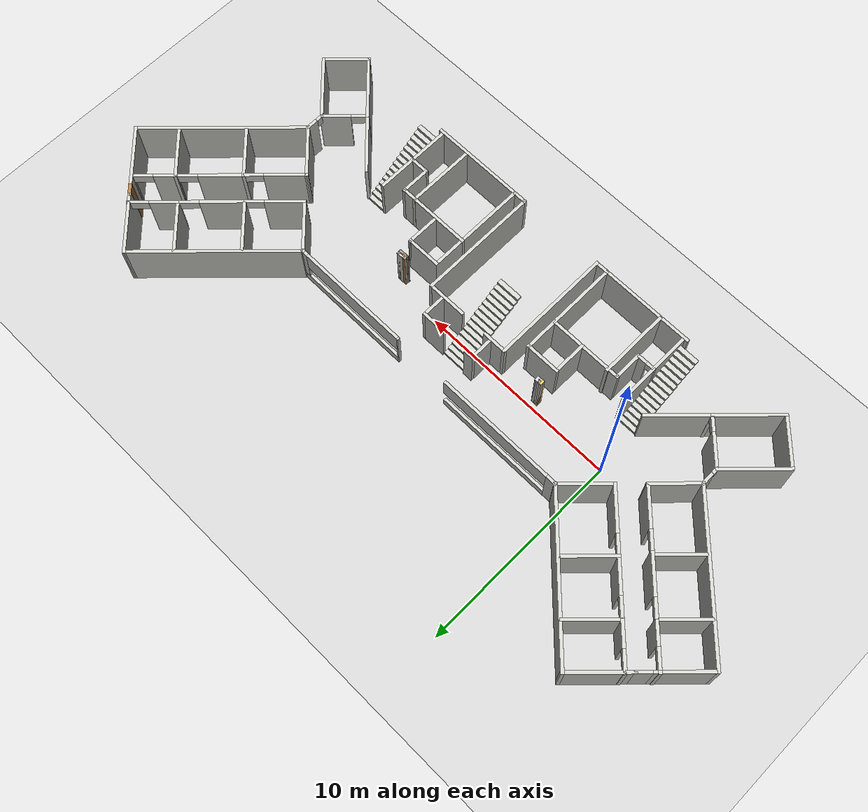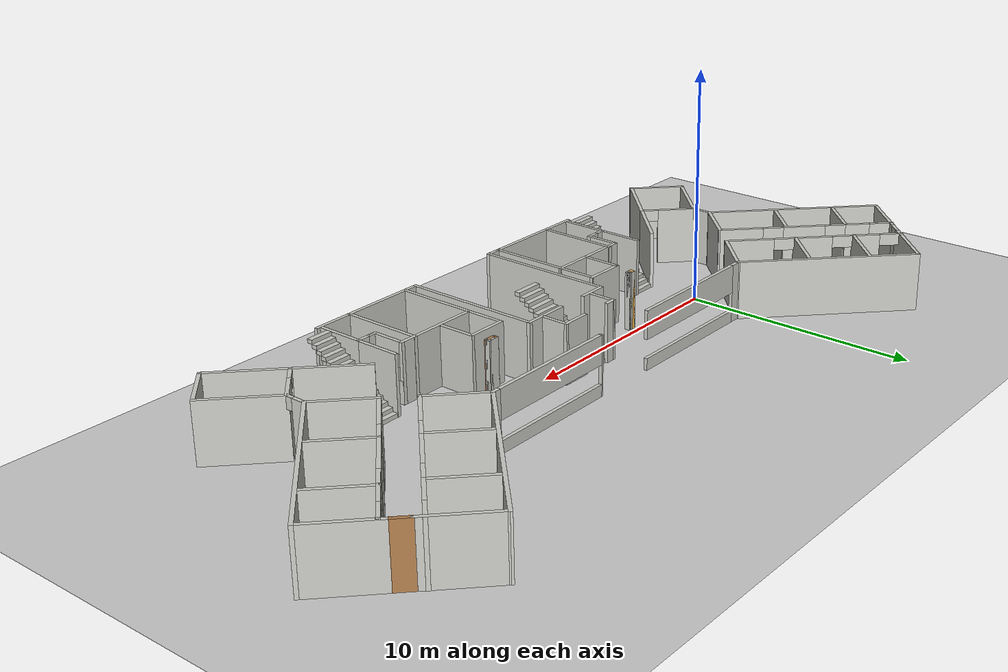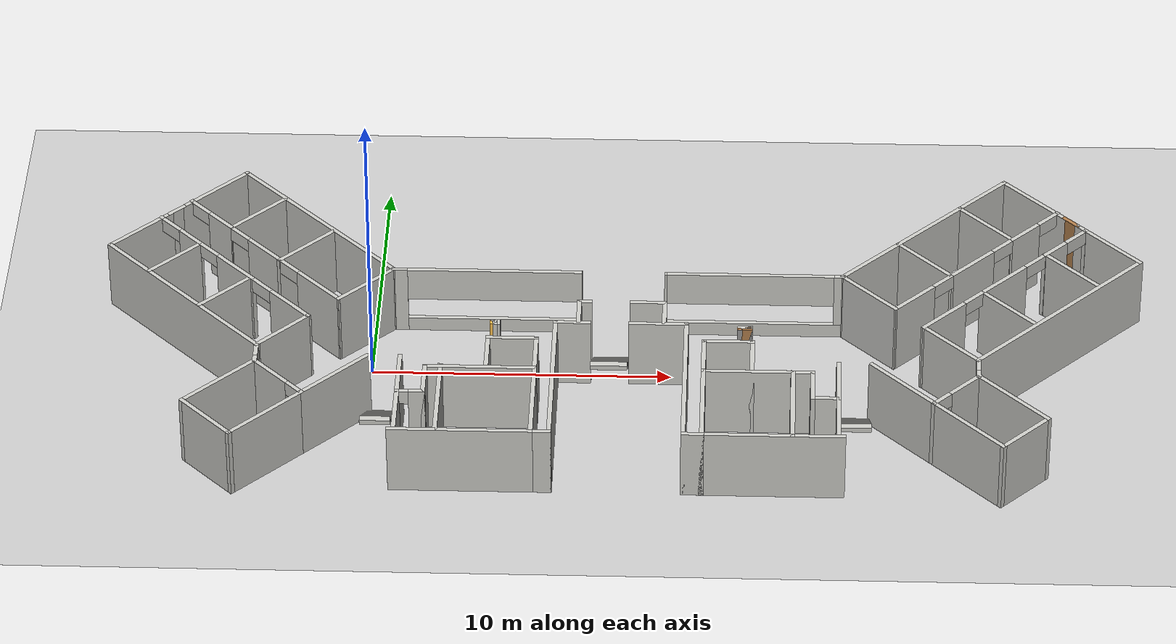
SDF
<sdf version="1.7">
 <world name="default">
  <light name="sun" type="directional">
   <pose>0 0 10 0 -0 0</pose>
   <diffuse>0.8 0.8 0.8 1</diffuse>
   <specular>0.2 0.2 0.2 1</specular>
   <attenuation>
    <range>1000</range>
    <constant>0.9</constant>
    <linear>0.01</linear>
    <quadratic>0.001</quadratic>
   </attenuation>
   <direction>-0.5 0.1 -0.9</direction>
   <spot><inner_angle>0</inner_angle><outer_angle>0</outer_angle><falloff>0</falloff></spot>
  </light>
  <model name="ground_plane">
   <static>1</static>
   <link name="link">
    <collision name="collision">
     <geometry><plane><normal>0 0 1</normal><size>100 100</size></plane></geometry>
     <surface>
      <contact><collide_bitmask>65535</collide_bitmask></contact>
      <friction><ode><mu>100</mu><mu2>50</mu2></ode></friction>
     </surface>
    </collision>
    <visual name="visual">
     <cast_shadows>0</cast_shadows>
     <geometry><plane><normal>0 0 1</normal><size>100 100</size></plane></geometry>
     <material>
      <script><uri>file://media/materials/scripts/gazebo.material</uri><name>Gazebo/Grey</name></script>
     </material>
    </visual>
   </link>
  </model>
  <gravity>0 0 -9.8</gravity>
  <magnetic_field>6e-06 2.3e-05 -4.2e-05</magnetic_field>
  <atmosphere type="adiabatic"/>
  <physics type="ode">
   <max_step_size>0.001</max_step_size>
   <real_time_factor>1</real_time_factor>
   <real_time_update_rate>1000</real_time_update_rate>
  </physics>
  <scene><ambient>0.4 0.4 0.4 1</ambient><background>0.7 0.7 0.7 1</background><shadows>1</shadows></scene>
  <spherical_coordinates>
   <surface_model>EARTH_WGS84</surface_model>
   <latitude_deg>0</latitude_deg>
   <longitude_deg>0</longitude_deg>
   <elevation>0</elevation>
   <heading_deg>0</heading_deg>
  </spherical_coordinates>
  <model name="SUST_IICT">
   <pose>8.32781 0.748146 0 0 -0 0</pose>
   <link name="Stairs_0">
    <visual name="Stairs_0_Visual_0">
     <pose>-0.342216 -0.026603 0.083333 0 -0 0</pose>
     <geometry><box><size>1.2128 0.233333 0.166667</size></box></geometry>
     <material>
      <script><uri>file://media/materials/scripts/gazebo.material</uri><name>Gazebo/CeilingTiled</name></script>
      <ambient>1 0.764706 0.305882 1</ambient>
     </material>
     <meta><layer>0</layer></meta>
    </visual>
    <collision name="Stairs_0_Collision_0">
     <geometry><box><size>1.2128 0.233333 0.166667</size></box></geometry>
     <pose>-0.342216 -0.026603 0.083333 0 -0 0</pose>
    </collision>
    <visual name="Stairs_0_Visual_1">
     <pose>-0.342216 -0.259936 0.25 0 -0 0</pose>
     <geometry><box><size>1.2128 0.233333 0.166667</size></box></geometry>
     <material>
      <script><uri>file://media/materials/scripts/gazebo.material</uri><name>Gazebo/CeilingTiled</name></script>
      <ambient>1 0.764706 0.305882 1</ambient>
     </material>
     <meta><layer>0</layer></meta>
    </visual>
    <collision name="Stairs_0_Collision_1">
     <geometry><box><size>1.2128 0.233333 0.166667</size></box></geometry>
     <pose>-0.342216 -0.259936 0.25 0 -0 0</pose>
    </collision>
    <visual name="Stairs_0_Visual_2">
     <pose>-0.342216 -0.49327 0.416667 0 -0 0</pose>
     <geometry><box><size>1.2128 0.233333 0.166667</size></box></geometry>
     <material>
      <script><uri>file://media/materials/scripts/gazebo.material</uri><name>Gazebo/CeilingTiled</name></script>
      <ambient>1 0.764706 0.305882 1</ambient>
     </material>
     <meta><layer>0</layer></meta>
    </visual>
    <collision name="Stairs_0_Collision_2">
     <geometry><box><size>1.2128 0.233333 0.166667</size></box></geometry>
     <pose>-0.342216 -0.49327 0.416667 0 -0 0</pose>
    </collision>
    <visual name="Stairs_0_Visual_3">
     <pose>-0.342216 -0.726603 0.583333 0 -0 0</pose>
     <geometry><box><size>1.2128 0.233333 0.166667</size></box></geometry>
     <material>
      <script><uri>file://media/materials/scripts/gazebo.material</uri><name>Gazebo/CeilingTiled</name></script>
      <ambient>1 0.764706 0.305882 1</ambient>
     </material>
     <meta><layer>0</layer></meta>
    </visual>
    <collision name="Stairs_0_Collision_3">
     <geometry><box><size>1.2128 0.233333 0.166667</size></box></geometry>
     <pose>-0.342216 -0.726603 0.583333 0 -0 0</pose>
    </collision>
    <visual name="Stairs_0_Visual_4">
     <pose>-0.342216 -0.959937 0.75 0 -0 0</pose>
     <geometry><box><size>1.2128 0.233333 0.166667</size></box></geometry>
     <material>
      <script><uri>file://media/materials/scripts/gazebo.material</uri><name>Gazebo/CeilingTiled</name></script>
      <ambient>1 0.764706 0.305882 1</ambient>
     </material>
     <meta><layer>0</layer></meta>
    </visual>
    <collision name="Stairs_0_Collision_4">
     <geometry><box><size>1.2128 0.233333 0.166667</size></box></geometry>
     <pose>-0.342216 -0.959937 0.75 0 -0 0</pose>
    </collision>
    <visual name="Stairs_0_Visual_5">
     <pose>-0.342216 -1.19327 0.916667 0 -0 0</pose>
     <geometry><box><size>1.2128 0.233333 0.166667</size></box></geometry>
     <material>
      <script><uri>file://media/materials/scripts/gazebo.material</uri><name>Gazebo/CeilingTiled</name></script>
      <ambient>1 0.764706 0.305882 1</ambient>
     </material>
     <meta><layer>0</layer></meta>
    </visual>
    <collision name="Stairs_0_Collision_5">
     <geometry><box><size>1.2128 0.233333 0.166667</size></box></geometry>
     <pose>-0.342216 -1.19327 0.916667 0 -0 0</pose>
    </collision>
    <visual name="Stairs_0_Visual_6">
     <pose>-0.342216 -1.4266 1.08333 0 -0 0</pose>
     <geometry><box><size>1.2128 0.233333 0.166667</size></box></geometry>
     <material>
      <script><uri>file://media/materials/scripts/gazebo.material</uri><name>Gazebo/CeilingTiled</name></script>
      <ambient>1 0.764706 0.305882 1</ambient>
     </material>
     <meta><layer>0</layer></meta>
    </visual>
    <collision name="Stairs_0_Collision_6">
     <geometry><box><size>1.2128 0.233333 0.166667</size></box></geometry>
     <pose>-0.342216 -1.4266 1.08333 0 -0 0</pose>
    </collision>
    <visual name="Stairs_0_Visual_7">
     <pose>-0.342216 -1.65994 1.25 0 -0 0</pose>
     <geometry><box><size>1.2128 0.233333 0.166667</size></box></geometry>
     <material>
      <script><uri>file://media/materials/scripts/gazebo.material</uri><name>Gazebo/CeilingTiled</name></script>
      <ambient>1 0.764706 0.305882 1</ambient>
     </material>
     <meta><layer>0</layer></meta>
    </visual>
    <collision name="Stairs_0_Collision_7">
     <geometry><box><size>1.2128 0.233333 0.166667</size></box></geometry>
     <pose>-0.342216 -1.65994 1.25 0 -0 0</pose>
    </collision>
    <visual name="Stairs_0_Visual_8">
     <pose>-0.342216 -1.89327 1.41667 0 -0 0</pose>
     <geometry><box><size>1.2128 0.233333 0.166667</size></box></geometry>
     <material>
      <script><uri>file://media/materials/scripts/gazebo.material</uri><name>Gazebo/CeilingTiled</name></script>
      <ambient>1 0.764706 0.305882 1</ambient>
     </material>
     <meta><layer>0</layer></meta>
    </visual>
    <collision name="Stairs_0_Collision_8">
     <geometry><box><size>1.2128 0.233333 0.166667</size></box></geometry>
     <pose>-0.342216 -1.89327 1.41667 0 -0 0</pose>
    </collision>
    <visual name="Stairs_0_Visual_9">
     <pose>-0.342216 -2.1266 1.58333 0 -0 0</pose>
     <geometry><box><size>1.2128 0.233333 0.166667</size></box></geometry>
     <material>
      <script><uri>file://media/materials/scripts/gazebo.material</uri><name>Gazebo/CeilingTiled</name></script>
      <ambient>1 0.764706 0.305882 1</ambient>
     </material>
     <meta><layer>0</layer></meta>
    </visual>
    <collision name="Stairs_0_Collision_9">
     <geometry><box><size>1.2128 0.233333 0.166667</size></box></geometry>
     <pose>-0.342216 -2.1266 1.58333 0 -0 0</pose>
    </collision>
    <visual name="Stairs_0_Visual_10">
     <pose>-0.342216 -2.35994 1.75 0 -0 0</pose>
     <geometry><box><size>1.2128 0.233333 0.166667</size></box></geometry>
     <material>
      <script><uri>file://media/materials/scripts/gazebo.material</uri><name>Gazebo/CeilingTiled</name></script>
      <ambient>1 0.764706 0.305882 1</ambient>
     </material>
     <meta><layer>0</layer></meta>
    </visual>
    <collision name="Stairs_0_Collision_10">
     <geometry><box><size>1.2128 0.233333 0.166667</size></box></geometry>
     <pose>-0.342216 -2.35994 1.75 0 -0 0</pose>
    </collision>
    <visual name="Stairs_0_Visual_11">
     <pose>-0.342216 -2.59327 1.91667 0 -0 0</pose>
     <geometry><box><size>1.2128 0.233333 0.166667</size></box></geometry>
     <material>
      <script><uri>file://media/materials/scripts/gazebo.material</uri><name>Gazebo/CeilingTiled</name></script>
      <ambient>1 0.764706 0.305882 1</ambient>
     </material>
     <meta><layer>0</layer></meta>
    </visual>
    <collision name="Stairs_0_Collision_11">
     <geometry><box><size>1.2128 0.233333 0.166667</size></box></geometry>
     <pose>-0.342216 -2.59327 1.91667 0 -0 0</pose>
    </collision>
    <visual name="Stairs_0_Visual_12">
     <pose>-0.342216 -2.8266 2.08333 0 -0 0</pose>
     <geometry><box><size>1.2128 0.233333 0.166667</size></box></geometry>
     <material>
      <script><uri>file://media/materials/scripts/gazebo.material</uri><name>Gazebo/CeilingTiled</name></script>
      <ambient>1 0.764706 0.305882 1</ambient>
     </material>
     <meta><layer>0</layer></meta>
    </visual>
    <collision name="Stairs_0_Collision_12">
     <geometry><box><size>1.2128 0.233333 0.166667</size></box></geometry>
     <pose>-0.342216 -2.8266 2.08333 0 -0 0</pose>
    </collision>
    <visual name="Stairs_0_Visual_13">
     <pose>-0.342216 -3.05994 2.25 0 -0 0</pose>
     <geometry><box><size>1.2128 0.233333 0.166667</size></box></geometry>
     <material>
      <script><uri>file://media/materials/scripts/gazebo.material</uri><name>Gazebo/CeilingTiled</name></script>
      <ambient>1 0.764706 0.305882 1</ambient>
     </material>
     <meta><layer>0</layer></meta>
    </visual>
    <collision name="Stairs_0_Collision_13">
     <geometry><box><size>1.2128 0.233333 0.166667</size></box></geometry>
     <pose>-0.342216 -3.05994 2.25 0 -0 0</pose>
    </collision>
    <visual name="Stairs_0_Visual_14">
     <pose>-0.342216 -3.29327 2.41667 0 -0 0</pose>
     <geometry><box><size>1.2128 0.233333 0.166667</size></box></geometry>
     <material>
      <script><uri>file://media/materials/scripts/gazebo.material</uri><name>Gazebo/CeilingTiled</name></script>
      <ambient>1 0.764706 0.305882 1</ambient>
     </material>
     <meta><layer>0</layer></meta>
    </visual>
    <collision name="Stairs_0_Collision_14">
     <geometry><box><size>1.2128 0.233333 0.166667</size></box></geometry>
     <pose>-0.342216 -3.29327 2.41667 0 -0 0</pose>
    </collision>
   </link>
   <link name="Stairs_1">
    <visual name="Stairs_1_Visual_0">
     <pose>-7.84347 -3.13883 0.083333 0 -0 0</pose>
     <geometry><box><size>1 0.233333 0.166667</size></box></geometry>
     <material>
      <script><uri>file://media/materials/scripts/gazebo.material</uri><name>Gazebo/CeilingTiled</name></script>
      <ambient>1 0.764706 0.305882 1</ambient>
     </material>
     <meta><layer>0</layer></meta>
    </visual>
    <collision name="Stairs_1_Collision_0">
     <geometry><box><size>1 0.233333 0.166667</size></box></geometry>
     <pose>-7.84347 -3.13883 0.083333 0 -0 0</pose>
    </collision>
    <visual name="Stairs_1_Visual_1">
     <pose>-7.84347 -3.37216 0.25 0 -0 0</pose>
     <geometry><box><size>1 0.233333 0.166667</size></box></geometry>
     <material>
      <script><uri>file://media/materials/scripts/gazebo.material</uri><name>Gazebo/CeilingTiled</name></script>
      <ambient>1 0.764706 0.305882 1</ambient>
     </material>
     <meta><layer>0</layer></meta>
    </visual>
    <collision name="Stairs_1_Collision_1">
     <geometry><box><size>1 0.233333 0.166667</size></box></geometry>
     <pose>-7.84347 -3.37216 0.25 0 -0 0</pose>
    </collision>
    <visual name="Stairs_1_Visual_2">
     <pose>-7.84347 -3.60549 0.416667 0 -0 0</pose>
     <geometry><box><size>1 0.233333 0.166667</size></box></geometry>
     <material>
      <script><uri>file://media/materials/scripts/gazebo.material</uri><name>Gazebo/CeilingTiled</name></script>
      <ambient>1 0.764706 0.305882 1</ambient>
     </material>
     <meta><layer>0</layer></meta>
    </visual>
    <collision name="Stairs_1_Collision_2">
     <geometry><box><size>1 0.233333 0.166667</size></box></geometry>
     <pose>-7.84347 -3.60549 0.416667 0 -0 0</pose>
    </collision>
    <visual name="Stairs_1_Visual_3">
     <pose>-7.84347 -3.83883 0.583333 0 -0 0</pose>
     <geometry><box><size>1 0.233333 0.166667</size></box></geometry>
     <material>
      <script><uri>file://media/materials/scripts/gazebo.material</uri><name>Gazebo/CeilingTiled</name></script>
      <ambient>1 0.764706 0.305882 1</ambient>
     </material>
     <meta><layer>0</layer></meta>
    </visual>
    <collision name="Stairs_1_Collision_3">
     <geometry><box><size>1 0.233333 0.166667</size></box></geometry>
     <pose>-7.84347 -3.83883 0.583333 0 -0 0</pose>
    </collision>
    <visual name="Stairs_1_Visual_4">
     <pose>-7.84347 -4.07216 0.75 0 -0 0</pose>
     <geometry><box><size>1 0.233333 0.166667</size></box></geometry>
     <material>
      <script><uri>file://media/materials/scripts/gazebo.material</uri><name>Gazebo/CeilingTiled</name></script>
      <ambient>1 0.764706 0.305882 1</ambient>
     </material>
     <meta><layer>0</layer></meta>
    </visual>
    <collision name="Stairs_1_Collision_4">
     <geometry><box><size>1 0.233333 0.166667</size></box></geometry>
     <pose>-7.84347 -4.07216 0.75 0 -0 0</pose>
    </collision>
    <visual name="Stairs_1_Visual_5">
     <pose>-7.84347 -4.30549 0.916667 0 -0 0</pose>
     <geometry><box><size>1 0.233333 0.166667</size></box></geometry>
     <material>
      <script><uri>file://media/materials/scripts/gazebo.material</uri><name>Gazebo/CeilingTiled</name></script>
      <ambient>1 0.764706 0.305882 1</ambient>
     </material>
     <meta><layer>0</layer></meta>
    </visual>
    <collision name="Stairs_1_Collision_5">
     <geometry><box><size>1 0.233333 0.166667</size></box></geometry>
     <pose>-7.84347 -4.30549 0.916667 0 -0 0</pose>
    </collision>
    <visual name="Stairs_1_Visual_6">
     <pose>-7.84347 -4.53883 1.08333 0 -0 0</pose>
     <geometry><box><size>1 0.233333 0.166667</size></box></geometry>
     <material>
      <script><uri>file://media/materials/scripts/gazebo.material</uri><name>Gazebo/CeilingTiled</name></script>
      <ambient>1 0.764706 0.305882 1</ambient>
     </material>
     <meta><layer>0</layer></meta>
    </visual>
    <collision name="Stairs_1_Collision_6">
     <geometry><box><size>1 0.233333 0.166667</size></box></geometry>
     <pose>-7.84347 -4.53883 1.08333 0 -0 0</pose>
    </collision>
    <visual name="Stairs_1_Visual_7">
     <pose>-7.84347 -4.77216 1.25 0 -0 0</pose>
     <geometry><box><size>1 0.233333 0.166667</size></box></geometry>
     <material>
      <script><uri>file://media/materials/scripts/gazebo.material</uri><name>Gazebo/CeilingTiled</name></script>
      <ambient>1 0.764706 0.305882 1</ambient>
     </material>
     <meta><layer>0</layer></meta>
    </visual>
    <collision name="Stairs_1_Collision_7">
     <geometry><box><size>1 0.233333 0.166667</size></box></geometry>
     <pose>-7.84347 -4.77216 1.25 0 -0 0</pose>
    </collision>
    <visual name="Stairs_1_Visual_8">
     <pose>-7.84347 -5.00549 1.41667 0 -0 0</pose>
     <geometry><box><size>1 0.233333 0.166667</size></box></geometry>
     <material>
      <script><uri>file://media/materials/scripts/gazebo.material</uri><name>Gazebo/CeilingTiled</name></script>
      <ambient>1 0.764706 0.305882 1</ambient>
     </material>
     <meta><layer>0</layer></meta>
    </visual>
    <collision name="Stairs_1_Collision_8">
     <geometry><box><size>1 0.233333 0.166667</size></box></geometry>
     <pose>-7.84347 -5.00549 1.41667 0 -0 0</pose>
    </collision>
    <visual name="Stairs_1_Visual_9">
     <pose>-7.84347 -5.23883 1.58333 0 -0 0</pose>
     <geometry><box><size>1 0.233333 0.166667</size></box></geometry>
     <material>
      <script><uri>file://media/materials/scripts/gazebo.material</uri><name>Gazebo/CeilingTiled</name></script>
      <ambient>1 0.764706 0.305882 1</ambient>
     </material>
     <meta><layer>0</layer></meta>
    </visual>
    <collision name="Stairs_1_Collision_9">
     <geometry><box><size>1 0.233333 0.166667</size></box></geometry>
     <pose>-7.84347 -5.23883 1.58333 0 -0 0</pose>
    </collision>
    <visual name="Stairs_1_Visual_10">
     <pose>-7.84347 -5.47216 1.75 0 -0 0</pose>
     <geometry><box><size>1 0.233333 0.166667</size></box></geometry>
     <material>
      <script><uri>file://media/materials/scripts/gazebo.material</uri><name>Gazebo/CeilingTiled</name></script>
      <ambient>1 0.764706 0.305882 1</ambient>
     </material>
     <meta><layer>0</layer></meta>
    </visual>
    <collision name="Stairs_1_Collision_10">
     <geometry><box><size>1 0.233333 0.166667</size></box></geometry>
     <pose>-7.84347 -5.47216 1.75 0 -0 0</pose>
    </collision>
    <visual name="Stairs_1_Visual_11">
     <pose>-7.84347 -5.70549 1.91667 0 -0 0</pose>
     <geometry><box><size>1 0.233333 0.166667</size></box></geometry>
     <material>
      <script><uri>file://media/materials/scripts/gazebo.material</uri><name>Gazebo/CeilingTiled</name></script>
      <ambient>1 0.764706 0.305882 1</ambient>
     </material>
     <meta><layer>0</layer></meta>
    </visual>
    <collision name="Stairs_1_Collision_11">
     <geometry><box><size>1 0.233333 0.166667</size></box></geometry>
     <pose>-7.84347 -5.70549 1.91667 0 -0 0</pose>
    </collision>
    <visual name="Stairs_1_Visual_12">
     <pose>-7.84347 -5.93883 2.08333 0 -0 0</pose>
     <geometry><box><size>1 0.233333 0.166667</size></box></geometry>
     <material>
      <script><uri>file://media/materials/scripts/gazebo.material</uri><name>Gazebo/CeilingTiled</name></script>
      <ambient>1 0.764706 0.305882 1</ambient>
     </material>
     <meta><layer>0</layer></meta>
    </visual>
    <collision name="Stairs_1_Collision_12">
     <geometry><box><size>1 0.233333 0.166667</size></box></geometry>
     <pose>-7.84347 -5.93883 2.08333 0 -0 0</pose>
    </collision>
    <visual name="Stairs_1_Visual_13">
     <pose>-7.84347 -6.17216 2.25 0 -0 0</pose>
     <geometry><box><size>1 0.233333 0.166667</size></box></geometry>
     <material>
      <script><uri>file://media/materials/scripts/gazebo.material</uri><name>Gazebo/CeilingTiled</name></script>
      <ambient>1 0.764706 0.305882 1</ambient>
     </material>
     <meta><layer>0</layer></meta>
    </visual>
    <collision name="Stairs_1_Collision_13">
     <geometry><box><size>1 0.233333 0.166667</size></box></geometry>
     <pose>-7.84347 -6.17216 2.25 0 -0 0</pose>
    </collision>
    <visual name="Stairs_1_Visual_14">
     <pose>-7.84347 -6.40549 2.41667 0 -0 0</pose>
     <geometry><box><size>1 0.233333 0.166667</size></box></geometry>
     <material>
      <script><uri>file://media/materials/scripts/gazebo.material</uri><name>Gazebo/CeilingTiled</name></script>
      <ambient>1 0.764706 0.305882 1</ambient>
     </material>
     <meta><layer>0</layer></meta>
    </visual>
    <collision name="Stairs_1_Collision_14">
     <geometry><box><size>1 0.233333 0.166667</size></box></geometry>
     <pose>-7.84347 -6.40549 2.41667 0 -0 0</pose>
    </collision>
   </link>
   <link name="Stairs_2">
    <visual name="Stairs_2_Visual_0">
     <pose>7.78414 -3.11134 0.083333 0 -0 0</pose>
     <geometry><box><size>0.9734 0.23156 0.166667</size></box></geometry>
     <material>
      <script><uri>file://media/materials/scripts/gazebo.material</uri><name>Gazebo/CeilingTiled</name></script>
      <ambient>1 0.764706 0.305882 1</ambient>
     </material>
     <meta><layer>0</layer></meta>
    </visual>
    <collision name="Stairs_2_Collision_0">
     <geometry><box><size>0.9734 0.23156 0.166667</size></box></geometry>
     <pose>7.78414 -3.11134 0.083333 0 -0 0</pose>
    </collision>
    <visual name="Stairs_2_Visual_1">
     <pose>7.78414 -3.3429 0.25 0 -0 0</pose>
     <geometry><box><size>0.9734 0.23156 0.166667</size></box></geometry>
     <material>
      <script><uri>file://media/materials/scripts/gazebo.material</uri><name>Gazebo/CeilingTiled</name></script>
      <ambient>1 0.764706 0.305882 1</ambient>
     </material>
     <meta><layer>0</layer></meta>
    </visual>
    <collision name="Stairs_2_Collision_1">
     <geometry><box><size>0.9734 0.23156 0.166667</size></box></geometry>
     <pose>7.78414 -3.3429 0.25 0 -0 0</pose>
    </collision>
    <visual name="Stairs_2_Visual_2">
     <pose>7.78414 -3.57446 0.416667 0 -0 0</pose>
     <geometry><box><size>0.9734 0.23156 0.166667</size></box></geometry>
     <material>
      <script><uri>file://media/materials/scripts/gazebo.material</uri><name>Gazebo/CeilingTiled</name></script>
      <ambient>1 0.764706 0.305882 1</ambient>
     </material>
     <meta><layer>0</layer></meta>
    </visual>
    <collision name="Stairs_2_Collision_2">
     <geometry><box><size>0.9734 0.23156 0.166667</size></box></geometry>
     <pose>7.78414 -3.57446 0.416667 0 -0 0</pose>
    </collision>
    <visual name="Stairs_2_Visual_3">
     <pose>7.78414 -3.80602 0.583333 0 -0 0</pose>
     <geometry><box><size>0.9734 0.23156 0.166667</size></box></geometry>
     <material>
      <script><uri>file://media/materials/scripts/gazebo.material</uri><name>Gazebo/CeilingTiled</name></script>
      <ambient>1 0.764706 0.305882 1</ambient>
     </material>
     <meta><layer>0</layer></meta>
    </visual>
    <collision name="Stairs_2_Collision_3">
     <geometry><box><size>0.9734 0.23156 0.166667</size></box></geometry>
     <pose>7.78414 -3.80602 0.583333 0 -0 0</pose>
    </collision>
    <visual name="Stairs_2_Visual_4">
     <pose>7.78414 -4.03758 0.75 0 -0 0</pose>
     <geometry><box><size>0.9734 0.23156 0.166667</size></box></geometry>
     <material>
      <script><uri>file://media/materials/scripts/gazebo.material</uri><name>Gazebo/CeilingTiled</name></script>
      <ambient>1 0.764706 0.305882 1</ambient>
     </material>
     <meta><layer>0</layer></meta>
    </visual>
    <collision name="Stairs_2_Collision_4">
     <geometry><box><size>0.9734 0.23156 0.166667</size></box></geometry>
     <pose>7.78414 -4.03758 0.75 0 -0 0</pose>
    </collision>
    <visual name="Stairs_2_Visual_5">
     <pose>7.78414 -4.26914 0.916667 0 -0 0</pose>
     <geometry><box><size>0.9734 0.23156 0.166667</size></box></geometry>
     <material>
      <script><uri>file://media/materials/scripts/gazebo.material</uri><name>Gazebo/CeilingTiled</name></script>
      <ambient>1 0.764706 0.305882 1</ambient>
     </material>
     <meta><layer>0</layer></meta>
    </visual>
    <collision name="Stairs_2_Collision_5">
     <geometry><box><size>0.9734 0.23156 0.166667</size></box></geometry>
     <pose>7.78414 -4.26914 0.916667 0 -0 0</pose>
    </collision>
    <visual name="Stairs_2_Visual_6">
     <pose>7.78414 -4.5007 1.08333 0 -0 0</pose>
     <geometry><box><size>0.9734 0.23156 0.166667</size></box></geometry>
     <material>
      <script><uri>file://media/materials/scripts/gazebo.material</uri><name>Gazebo/CeilingTiled</name></script>
      <ambient>1 0.764706 0.305882 1</ambient>
     </material>
     <meta><layer>0</layer></meta>
    </visual>
    <collision name="Stairs_2_Collision_6">
     <geometry><box><size>0.9734 0.23156 0.166667</size></box></geometry>
     <pose>7.78414 -4.5007 1.08333 0 -0 0</pose>
    </collision>
    <visual name="Stairs_2_Visual_7">
     <pose>7.78414 -4.73226 1.25 0 -0 0</pose>
     <geometry><box><size>0.9734 0.23156 0.166667</size></box></geometry>
     <material>
      <script><uri>file://media/materials/scripts/gazebo.material</uri><name>Gazebo/CeilingTiled</name></script>
      <ambient>1 0.764706 0.305882 1</ambient>
     </material>
     <meta><layer>0</layer></meta>
    </visual>
    <collision name="Stairs_2_Collision_7">
     <geometry><box><size>0.9734 0.23156 0.166667</size></box></geometry>
     <pose>7.78414 -4.73226 1.25 0 -0 0</pose>
    </collision>
    <visual name="Stairs_2_Visual_8">
     <pose>7.78414 -4.96382 1.41667 0 -0 0</pose>
     <geometry><box><size>0.9734 0.23156 0.166667</size></box></geometry>
     <material>
      <script><uri>file://media/materials/scripts/gazebo.material</uri><name>Gazebo/CeilingTiled</name></script>
      <ambient>1 0.764706 0.305882 1</ambient>
     </material>
     <meta><layer>0</layer></meta>
    </visual>
    <collision name="Stairs_2_Collision_8">
     <geometry><box><size>0.9734 0.23156 0.166667</size></box></geometry>
     <pose>7.78414 -4.96382 1.41667 0 -0 0</pose>
    </collision>
    <visual name="Stairs_2_Visual_9">
     <pose>7.78414 -5.19538 1.58333 0 -0 0</pose>
     <geometry><box><size>0.9734 0.23156 0.166667</size></box></geometry>
     <material>
      <script><uri>file://media/materials/scripts/gazebo.material</uri><name>Gazebo/CeilingTiled</name></script>
      <ambient>1 0.764706 0.305882 1</ambient>
     </material>
     <meta><layer>0</layer></meta>
    </visual>
    <collision name="Stairs_2_Collision_9">
     <geometry><box><size>0.9734 0.23156 0.166667</size></box></geometry>
     <pose>7.78414 -5.19538 1.58333 0 -0 0</pose>
    </collision>
    <visual name="Stairs_2_Visual_10">
     <pose>7.78414 -5.42694 1.75 0 -0 0</pose>
     <geometry><box><size>0.9734 0.23156 0.166667</size></box></geometry>
     <material>
      <script><uri>file://media/materials/scripts/gazebo.material</uri><name>Gazebo/CeilingTiled</name></script>
      <ambient>1 0.764706 0.305882 1</ambient>
     </material>
     <meta><layer>0</layer></meta>
    </visual>
    <collision name="Stairs_2_Collision_10">
     <geometry><box><size>0.9734 0.23156 0.166667</size></box></geometry>
     <pose>7.78414 -5.42694 1.75 0 -0 0</pose>
    </collision>
    <visual name="Stairs_2_Visual_11">
     <pose>7.78414 -5.6585 1.91667 0 -0 0</pose>
     <geometry><box><size>0.9734 0.23156 0.166667</size></box></geometry>
     <material>
      <script><uri>file://media/materials/scripts/gazebo.material</uri><name>Gazebo/CeilingTiled</name></script>
      <ambient>1 0.764706 0.305882 1</ambient>
     </material>
     <meta><layer>0</layer></meta>
    </visual>
    <collision name="Stairs_2_Collision_11">
     <geometry><box><size>0.9734 0.23156 0.166667</size></box></geometry>
     <pose>7.78414 -5.6585 1.91667 0 -0 0</pose>
    </collision>
    <visual name="Stairs_2_Visual_12">
     <pose>7.78414 -5.89006 2.08333 0 -0 0</pose>
     <geometry><box><size>0.9734 0.23156 0.166667</size></box></geometry>
     <material>
      <script><uri>file://media/materials/scripts/gazebo.material</uri><name>Gazebo/CeilingTiled</name></script>
      <ambient>1 0.764706 0.305882 1</ambient>
     </material>
     <meta><layer>0</layer></meta>
    </visual>
    <collision name="Stairs_2_Collision_12">
     <geometry><box><size>0.9734 0.23156 0.166667</size></box></geometry>
     <pose>7.78414 -5.89006 2.08333 0 -0 0</pose>
    </collision>
    <visual name="Stairs_2_Visual_13">
     <pose>7.78414 -6.12162 2.25 0 -0 0</pose>
     <geometry><box><size>0.9734 0.23156 0.166667</size></box></geometry>
     <material>
      <script><uri>file://media/materials/scripts/gazebo.material</uri><name>Gazebo/CeilingTiled</name></script>
      <ambient>1 0.764706 0.305882 1</ambient>
     </material>
     <meta><layer>0</layer></meta>
    </visual>
    <collision name="Stairs_2_Collision_13">
     <geometry><box><size>0.9734 0.23156 0.166667</size></box></geometry>
     <pose>7.78414 -6.12162 2.25 0 -0 0</pose>
    </collision>
    <visual name="Stairs_2_Visual_14">
     <pose>7.78414 -6.35318 2.41667 0 -0 0</pose>
     <geometry><box><size>0.9734 0.23156 0.166667</size></box></geometry>
     <material>
      <script><uri>file://media/materials/scripts/gazebo.material</uri><name>Gazebo/CeilingTiled</name></script>
      <ambient>1 0.764706 0.305882 1</ambient>
     </material>
     <meta><layer>0</layer></meta>
    </visual>
    <collision name="Stairs_2_Collision_14">
     <geometry><box><size>0.9734 0.23156 0.166667</size></box></geometry>
     <pose>7.78414 -6.35318 2.41667 0 -0 0</pose>
    </collision>
   </link>
   <link name="Wall_100">
    <collision name="Wall_100_Collision">
     <geometry><box><size>2.5 0.15 2.5</size></box></geometry>
     <pose>0 0 1.25 0 -0 0</pose>
    </collision>
    <visual name="Wall_100_Visual">
     <pose>0 0 1.25 0 -0 0</pose>
     <geometry><box><size>2.5 0.15 2.5</size></box></geometry>
     <material>
      <script><uri>file://media/materials/scripts/gazebo.material</uri><name>Gazebo/CeilingTiled</name></script>
      <ambient>1 0.764706 0.305882 1</ambient>
     </material>
     <meta><layer>0</layer></meta>
    </visual>
    <pose>-13.3631 -6.43541 0 0 -0 2.35619</pose>
   </link>
   <link name="Wall_102">
    <collision name="Wall_102_Collision">
     <geometry><box><size>3.25 0.15 2.5</size></box></geometry>
     <pose>0 0 1.25 0 -0 0</pose>
    </collision>
    <visual name="Wall_102_Visual">
     <pose>0 0 1.25 0 -0 0</pose>
     <geometry><box><size>3.25 0.15 2.5</size></box></geometry>
     <material>
      <script><uri>file://media/materials/scripts/gazebo.material</uri><name>Gazebo/CeilingTiled</name></script>
      <ambient>1 0.764706 0.305882 1</ambient>
     </material>
     <meta><layer>0</layer></meta>
    </visual>
    <pose>-13.098 -4.50854 0 0 -0 0.785398</pose>
   </link>
   <link name="Wall_107">
    <collision name="Wall_107_Collision">
     <geometry><box><size>3 0.15 2.5</size></box></geometry>
     <pose>0 0 1.25 0 -0 0</pose>
    </collision>
    <visual name="Wall_107_Visual">
     <pose>0 0 1.25 0 -0 0</pose>
     <geometry><box><size>3 0.15 2.5</size></box></geometry>
     <material>
      <script><uri>file://media/materials/scripts/gazebo.material</uri><name>Gazebo/CeilingTiled</name></script>
      <ambient>1 0.764706 0.305882 1</ambient>
     </material>
     <meta><layer>0</layer></meta>
    </visual>
    <pose>13.9288 6.25863 0 0 -0 2.35619</pose>
   </link>
   <link name="Wall_112">
    <collision name="Wall_112_Collision">
     <geometry><box><size>8 0.15 2.5</size></box></geometry>
     <pose>0 0 1.25 0 -0 0</pose>
    </collision>
    <visual name="Wall_112_Visual">
     <pose>0 0 1.25 0 -0 0</pose>
     <geometry><box><size>8 0.15 2.5</size></box></geometry>
     <material>
      <script><uri>file://media/materials/scripts/gazebo.material</uri><name>Gazebo/CeilingTiled</name></script>
      <ambient>1 0.764706 0.305882 1</ambient>
     </material>
     <meta><layer>0</layer></meta>
    </visual>
    <pose>14.6006 0.036092 0 0 -0 0.785398</pose>
   </link>
   <link name="Wall_114">
    <collision name="Wall_114_Collision">
     <geometry><box><size>7.99602 0.15 2.5</size></box></geometry>
     <pose>0 0 1.25 0 -0 0</pose>
    </collision>
    <visual name="Wall_114_Visual">
     <pose>0 0 1.25 0 -0 0</pose>
     <geometry><box><size>7.99602 0.15 2.5</size></box></geometry>
     <material>
      <script><uri>file://media/materials/scripts/gazebo.material</uri><name>Gazebo/CeilingTiled</name></script>
      <ambient>1 0.764706 0.305882 1</ambient>
     </material>
     <meta><layer>0</layer></meta>
    </visual>
    <pose>10.1486 4.49086 0 0 -0 0.785906</pose>
   </link>
   <link name="Wall_116">
    <collision name="Wall_116_Collision">
     <geometry><box><size>3 0.15 2.5</size></box></geometry>
     <pose>0 0 1.25 0 -0 0</pose>
    </collision>
    <visual name="Wall_116_Visual">
     <pose>0 0 1.25 0 -0 0</pose>
     <geometry><box><size>3 0.15 2.5</size></box></geometry>
     <material>
      <script><uri>file://media/materials/scripts/gazebo.material</uri><name>Gazebo/CeilingTiled</name></script>
      <ambient>1 0.764706 0.305882 1</ambient>
     </material>
     <meta><layer>0</layer></meta>
    </visual>
    <pose>16.3683 3.81911 0 0 -0 -0.785398</pose>
   </link>
   <link name="Wall_118">
    <collision name="Wall_118_Collision">
     <geometry><box><size>4.75 0.15 2.5</size></box></geometry>
     <pose>0 0 1.25 0 -0 0</pose>
    </collision>
    <visual name="Wall_118_Visual">
     <pose>0 0 1.25 0 -0 0</pose>
     <geometry><box><size>4.75 0.15 2.5</size></box></geometry>
     <material>
      <script><uri>file://media/materials/scripts/gazebo.material</uri><name>Gazebo/CeilingTiled</name></script>
      <ambient>1 0.764706 0.305882 1</ambient>
     </material>
     <meta><layer>0</layer></meta>
    </visual>
    <pose>-5.075 -6.90897 0 0 -0 3.14159</pose>
   </link>
   <link name="Wall_128">
    <collision name="Wall_128_Collision">
     <geometry><box><size>2 0.15 2.5</size></box></geometry>
     <pose>0 0 1.25 0 -0 0</pose>
    </collision>
    <visual name="Wall_128_Visual">
     <pose>0 0 1.25 0 -0 0</pose>
     <geometry><box><size>2 0.15 2.5</size></box></geometry>
     <material>
      <script><uri>file://media/materials/scripts/gazebo.material</uri><name>Gazebo/CeilingTiled</name></script>
      <ambient>1 0.764706 0.305882 1</ambient>
     </material>
     <meta><layer>0</layer></meta>
    </visual>
    <pose>-7.225 -5.83397 0 0 -0 -1.5708</pose>
   </link>
   <link name="Wall_130">
    <collision name="Wall_130_Collision">
     <geometry><box><size>2 0.15 2.5</size></box></geometry>
     <pose>0 0 1.25 0 -0 0</pose>
    </collision>
    <visual name="Wall_130_Visual">
     <pose>0 0 1.25 0 -0 0</pose>
     <geometry><box><size>2 0.15 2.5</size></box></geometry>
     <material>
      <script><uri>file://media/materials/scripts/gazebo.material</uri><name>Gazebo/CeilingTiled</name></script>
      <ambient>1 0.764706 0.305882 1</ambient>
     </material>
     <meta><layer>0</layer></meta>
    </visual>
    <pose>7.225 -5.83397 0 0 -0 -1.5708</pose>
   </link>
   <link name="Wall_136">
    <collision name="Wall_136_Collision">
     <geometry><box><size>3.25 0.15 2.5</size></box></geometry>
     <pose>0 0 1.25 0 -0 0</pose>
    </collision>
    <visual name="Wall_136_Visual">
     <pose>0 0 1.25 0 -0 0</pose>
     <geometry><box><size>3.25 0.15 2.5</size></box></geometry>
     <material>
      <script><uri>file://media/materials/scripts/gazebo.material</uri><name>Gazebo/CeilingTiled</name></script>
      <ambient>1 0.764706 0.305882 1</ambient>
     </material>
     <meta><layer>0</layer></meta>
    </visual>
    <pose>11.4363 -6.17024 0 0 -0 -0.785398</pose>
   </link>
   <link name="Wall_141">
    <collision name="Wall_141_Collision">
     <geometry><box><size>3.25 0.15 2.5</size></box></geometry>
     <pose>0 0 1.25 0 -0 0</pose>
    </collision>
    <visual name="Wall_141_Visual">
     <pose>0 0 1.25 0 -0 0</pose>
     <geometry><box><size>3.25 0.15 2.5</size></box></geometry>
     <material>
      <script><uri>file://media/materials/scripts/gazebo.material</uri><name>Gazebo/CeilingTiled</name></script>
      <ambient>1 0.764706 0.305882 1</ambient>
     </material>
     <meta><layer>0</layer></meta>
    </visual>
    <pose>12.9212 -4.68532 0 0 -0 -0.785398</pose>
   </link>
   <link name="Wall_143">
    <collision name="Wall_143_Collision">
     <geometry><box><size>2.25 0.15 2.5</size></box></geometry>
     <pose>0 0 1.25 0 -0 0</pose>
    </collision>
    <visual name="Wall_143_Visual">
     <pose>0 0 1.25 0 -0 0</pose>
     <geometry><box><size>2.25 0.15 2.5</size></box></geometry>
     <material>
      <script><uri>file://media/materials/scripts/gazebo.material</uri><name>Gazebo/CeilingTiled</name></script>
      <ambient>1 0.764706 0.305882 1</ambient>
     </material>
     <meta><layer>0</layer></meta>
    </visual>
    <pose>13.2747 -6.5238 0 0 -0 0.785398</pose>
   </link>
   <link name="Wall_145">
    <collision name="Wall_145_Collision">
     <geometry><box><size>4.75 0.15 2.5</size></box></geometry>
     <pose>0 0 1.25 0 -0 0</pose>
    </collision>
    <visual name="Wall_145_Visual">
     <pose>0 0 1.25 0 -0 0</pose>
     <geometry><box><size>4.75 0.15 2.5</size></box></geometry>
     <material>
      <script><uri>file://media/materials/scripts/gazebo.material</uri><name>Gazebo/CeilingTiled</name></script>
      <ambient>1 0.764706 0.305882 1</ambient>
     </material>
     <meta><layer>0</layer></meta>
    </visual>
    <pose>5.075 -6.90897 0 0 -0 0</pose>
   </link>
   <link name="Wall_147">
    <collision name="Wall_147_Collision">
     <geometry><box><size>0.5 0.15 2.5</size></box></geometry>
     <pose>0 0 1.25 0 -0 0</pose>
    </collision>
    <visual name="Wall_147_Visual">
     <pose>0 0 1.25 0 -0 0</pose>
     <geometry><box><size>0.5 0.15 2.5</size></box></geometry>
     <material>
      <script><uri>file://media/materials/scripts/gazebo.material</uri><name>Gazebo/CeilingTiled</name></script>
      <ambient>1 0.764706 0.305882 1</ambient>
     </material>
     <meta><layer>0</layer></meta>
    </visual>
    <pose>-1.24107 0.100337 0 0 -0 0</pose>
   </link>
   <link name="Wall_149">
    <collision name="Wall_149_Collision">
     <geometry><box><size>1.25 0.15 2.5</size></box></geometry>
     <pose>0 0 1.25 0 -0 0</pose>
    </collision>
    <visual name="Wall_149_Visual">
     <pose>0 0 1.25 0 -0 0</pose>
     <geometry><box><size>1.25 0.15 2.5</size></box></geometry>
     <material>
      <script><uri>file://media/materials/scripts/gazebo.material</uri><name>Gazebo/CeilingTiled</name></script>
      <ambient>1 0.764706 0.305882 1</ambient>
     </material>
     <meta><layer>0</layer></meta>
    </visual>
    <pose>0.883935 0.100337 0 0 -0 3.14159</pose>
   </link>
   <link name="Wall_151">
    <collision name="Wall_151_Collision">
     <geometry><box><size>1.25 0.15 2.5</size></box></geometry>
     <pose>0 0 1.25 0 -0 0</pose>
    </collision>
    <visual name="Wall_151_Visual">
     <pose>0 0 1.25 0 -0 0</pose>
     <geometry><box><size>1.25 0.15 2.5</size></box></geometry>
     <material>
      <script><uri>file://media/materials/scripts/gazebo.material</uri><name>Gazebo/CeilingTiled</name></script>
      <ambient>1 0.764706 0.305882 1</ambient>
     </material>
     <meta><layer>0</layer></meta>
    </visual>
    <pose>-1.625 -1.05897 0 0 -0 0</pose>
   </link>
   <link name="Wall_157">
    <collision name="Wall_157_Collision">
     <geometry><box><size>2 0.15 2.5</size></box></geometry>
     <pose>0 0 1.25 0 -0 0</pose>
    </collision>
    <visual name="Wall_157_Visual">
     <pose>0 0 1.25 0 -0 0</pose>
     <geometry><box><size>2 0.15 2.5</size></box></geometry>
     <material>
      <script><uri>file://media/materials/scripts/gazebo.material</uri><name>Gazebo/CeilingTiled</name></script>
      <ambient>1 0.764706 0.305882 1</ambient>
     </material>
     <meta><layer>0</layer></meta>
    </visual>
    <pose>1.25 -1.05897 0 0 -0 3.14159</pose>
   </link>
   <link name="Wall_176">
    <collision name="Wall_176_Collision">
     <geometry><box><size>0.25 0.15 2.5</size></box></geometry>
     <pose>0 0 1.25 0 -0 0</pose>
    </collision>
    <visual name="Wall_176_Visual">
     <pose>0 0 1.25 0 -0 0</pose>
     <geometry><box><size>0.25 0.15 2.5</size></box></geometry>
     <material>
      <script><uri>file://media/materials/scripts/gazebo.material</uri><name>Gazebo/Grey</name></script>
      <ambient>1 0.764706 0.305882 1</ambient>
     </material>
     <meta><layer>0</layer></meta>
    </visual>
    <pose>-4.27904 -1.12473 0 0 -0 -1.5708</pose>
   </link>
   <link name="Wall_18">
    <collision name="Wall_18_Collision">
     <geometry><box><size>0.75 0.15 2.5</size></box></geometry>
     <pose>0 0 1.25 0 -0 0</pose>
    </collision>
    <visual name="Wall_18_Visual">
     <pose>0 0 1.25 0 -0 0</pose>
     <geometry><box><size>0.75 0.15 2.5</size></box></geometry>
     <material>
      <script><uri>file://media/materials/scripts/gazebo.material</uri><name>Gazebo/Wood</name></script>
      <ambient>1 1 1 1</ambient>
     </material>
     <meta><layer>0</layer></meta>
    </visual>
    <pose>15.1486 5.03887 0 0 -0 -0.785398</pose>
   </link>
   <link name="Wall_180">
    <collision name="Wall_180_Collision">
     <geometry><box><size>0.25 0.15 2.5</size></box></geometry>
     <pose>0 0 1.25 0 -0 0</pose>
    </collision>
    <visual name="Wall_180_Visual">
     <pose>0 0 1.25 0 -0 0</pose>
     <geometry><box><size>0.25 0.15 2.5</size></box></geometry>
     <material>
      <script><uri>file://media/materials/scripts/gazebo.material</uri><name>Gazebo/CeilingTiled</name></script>
      <ambient>1 1 1 1</ambient>
     </material>
     <meta><layer>0</layer></meta>
    </visual>
    <pose>-4.22905 -1.07473 0 0 -0 0</pose>
   </link>
   <link name="Wall_181">
    <collision name="Wall_181_Collision">
     <geometry><box><size>0.25 0.15 2.5</size></box></geometry>
     <pose>0 0 1.25 0 -0 0</pose>
    </collision>
    <visual name="Wall_181_Visual">
     <pose>0 0 1.25 0 -0 0</pose>
     <geometry><box><size>0.25 0.15 2.5</size></box></geometry>
     <material>
      <script><uri>file://media/materials/scripts/gazebo.material</uri><name>Gazebo/Grey</name></script>
      <ambient>1 1 1 1</ambient>
     </material>
     <meta><layer>0</layer></meta>
    </visual>
    <pose>-4.22905 -1.07473 0 0 -0 3.14159</pose>
   </link>
   <link name="Wall_183">
    <collision name="Wall_183_Collision">
     <geometry><box><size>0.25 0.15 2.5</size></box></geometry>
     <pose>0 0 1.25 0 -0 0</pose>
    </collision>
    <visual name="Wall_183_Visual">
     <pose>0 0 1.25 0 -0 0</pose>
     <geometry><box><size>0.25 0.15 2.5</size></box></geometry>
     <material>
      <script><uri>file://media/materials/scripts/gazebo.material</uri><name>Gazebo/CeilingTiled</name></script>
      <ambient>0.996078 0.47451 0.0196078 1</ambient>
     </material>
     <meta><layer>0</layer></meta>
    </visual>
    <pose>-4.22905 -1.07473 0 0 -0 3.14159</pose>
   </link>
   <link name="Wall_185">
    <collision name="Wall_185_Collision">
     <geometry><box><size>0.25 0.15 2.5</size></box></geometry>
     <pose>0 0 1.25 0 -0 0</pose>
    </collision>
    <visual name="Wall_185_Visual">
     <pose>0 0 1.25 0 -0 0</pose>
     <geometry><box><size>0.25 0.15 2.5</size></box></geometry>
     <material>
      <script><uri>file://media/materials/scripts/gazebo.material</uri><name>Gazebo/CeilingTiled</name></script>
      <ambient>1 0.764706 0.305882 1</ambient>
     </material>
     <meta><layer>0</layer></meta>
    </visual>
    <pose>-4.17905 -1.12473 0 0 -0 -1.5708</pose>
   </link>
   <link name="Wall_199">
    <collision name="Wall_199_Collision">
     <geometry><box><size>0.25 0.15 2.5</size></box></geometry>
     <pose>0 0 1.25 0 -0 0</pose>
    </collision>
    <visual name="Wall_199_Visual">
     <pose>0 0 1.25 0 -0 0</pose>
     <geometry><box><size>0.25 0.15 2.5</size></box></geometry>
     <material>
      <script><uri>file://media/materials/scripts/gazebo.material</uri><name>Gazebo/Grey</name></script>
      <ambient>1 1 1 1</ambient>
     </material>
     <meta><layer>0</layer></meta>
    </visual>
    <pose>-4.12904 -1.07473 0 0 -0 0</pose>
   </link>
   <link name="Wall_200">
    <collision name="Wall_200_Collision">
     <geometry><box><size>0.25 0.15 2.5</size></box></geometry>
     <pose>0 0 1.25 0 -0 0</pose>
    </collision>
    <visual name="Wall_200_Visual">
     <pose>0 0 1.25 0 -0 0</pose>
     <geometry><box><size>0.25 0.15 2.5</size></box></geometry>
     <material>
      <script><uri>file://media/materials/scripts/gazebo.material</uri><name>Gazebo/Grey</name></script>
      <ambient>1 1 1 1</ambient>
     </material>
     <meta><layer>0</layer></meta>
    </visual>
    <pose>-4.12904 -1.07473 0 0 -0 3.14159</pose>
   </link>
   <link name="Wall_201">
    <collision name="Wall_201_Collision">
     <geometry><box><size>0.25 0.15 2.5</size></box></geometry>
     <pose>0 0 1.25 0 -0 0</pose>
    </collision>
    <visual name="Wall_201_Visual">
     <pose>0 0 1.25 0 -0 0</pose>
     <geometry><box><size>0.25 0.15 2.5</size></box></geometry>
     <material>
      <script><uri>file://media/materials/scripts/gazebo.material</uri><name>Gazebo/Wood</name></script>
      <ambient>1 0.764706 0.305882 1</ambient>
     </material>
     <meta><layer>0</layer></meta>
    </visual>
    <pose>-4.12904 -1.07473 0 0 -0 0</pose>
   </link>
   <link name="Wall_202">
    <collision name="Wall_202_Collision">
     <geometry><box><size>0.25 0.15 2.5</size></box></geometry>
     <pose>0 0 1.25 0 -0 0</pose>
    </collision>
    <visual name="Wall_202_Visual">
     <pose>0 0 1.25 0 -0 0</pose>
     <geometry><box><size>0.25 0.15 2.5</size></box></geometry>
     <material>
      <script><uri>file://media/materials/scripts/gazebo.material</uri><name>Gazebo/Grey</name></script>
      <ambient>1 1 1 1</ambient>
     </material>
     <meta><layer>0</layer></meta>
    </visual>
    <pose>-4.12904 -1.07473 0 0 -0 3.14159</pose>
   </link>
   <link name="Wall_204">
    <collision name="Wall_204_Collision">
     <geometry><box><size>0.25 0.15 2.5</size></box></geometry>
     <pose>0 0 1.25 0 -0 0</pose>
    </collision>
    <visual name="Wall_204_Visual">
     <pose>0 0 1.25 0 -0 0</pose>
     <geometry><box><size>0.25 0.15 2.5</size></box></geometry>
     <material>
      <script><uri>file://media/materials/scripts/gazebo.material</uri><name>Gazebo/CeilingTiled</name></script>
      <ambient>1 0.764706 0.305882 1</ambient>
     </material>
     <meta><layer>0</layer></meta>
    </visual>
    <pose>-4.12904 -1.07473 0 0 -0 3.14159</pose>
   </link>
   <link name="Wall_206">
    <collision name="Wall_206_Collision">
     <geometry><box><size>0.25 0.15 2.5</size></box></geometry>
     <pose>0 0 1.25 0 -0 0</pose>
    </collision>
    <visual name="Wall_206_Visual">
     <pose>0 0 1.25 0 -0 0</pose>
     <geometry><box><size>0.25 0.15 2.5</size></box></geometry>
     <material>
      <script><uri>file://media/materials/scripts/gazebo.material</uri><name>Gazebo/CeilingTiled</name></script>
      <ambient>1 0.764706 0.305882 1</ambient>
     </material>
     <meta><layer>0</layer></meta>
    </visual>
    <pose>-4.07904 -1.12473 0 0 -0 -1.5708</pose>
   </link>
   <link name="Wall_21">
    <pose>11.8252 -3.1643 0 0 -0 -1.5708</pose>
    <visual name="Wall_21_Visual_0">
     <pose>-0.193916 0 1.25 0 -0 0</pose>
     <geometry><box><size>0.612167 0.15 2.5</size></box></geometry>
     <material>
      <script><uri>file://media/materials/scripts/gazebo.material</uri><name>Gazebo/CeilingTiled</name></script>
      <ambient>1 0.764706 0.305882 1</ambient>
     </material>
     <meta><layer>0</layer></meta>
    </visual>
    <collision name="Wall_21_Collision_0">
     <geometry><box><size>0.612167 0.15 2.5</size></box></geometry>
     <pose>-0.193916 0 1.25 0 -0 0</pose>
    </collision>
    <visual name="Wall_21_Visual_1">
     <pose>0.476781 0 1.25 0 -0 0</pose>
     <geometry><box><size>0.046437 0.15 2.5</size></box></geometry>
     <material>
      <script><uri>file://media/materials/scripts/gazebo.material</uri><name>Gazebo/CeilingTiled</name></script>
      <ambient>1 0.764706 0.305882 1</ambient>
     </material>
     <meta><layer>0</layer></meta>
    </visual>
    <collision name="Wall_21_Collision_1">
     <geometry><box><size>0.046437 0.15 2.5</size></box></geometry>
     <pose>0.476781 0 1.25 0 -0 0</pose>
    </collision>
    <visual name="Wall_21_Visual_2">
     <pose>0.282865 0 2.25 0 -0 0</pose>
     <geometry><box><size>0.341396 0.15 0.5</size></box></geometry>
     <material>
      <script><uri>file://media/materials/scripts/gazebo.material</uri><name>Gazebo/CeilingTiled</name></script>
      <ambient>1 0.764706 0.305882 1</ambient>
     </material>
     <meta><layer>0</layer></meta>
    </visual>
    <collision name="Wall_21_Collision_2">
     <geometry><box><size>0.341396 0.15 0.5</size></box></geometry>
     <pose>0.282865 0 2.25 0 -0 0</pose>
    </collision>
   </link>
   <link name="Wall_219">
    <collision name="Wall_219_Collision">
     <geometry><box><size>0.25 0.15 2.5</size></box></geometry>
     <pose>0 0 1.25 0 -0 0</pose>
    </collision>
    <visual name="Wall_219_Visual">
     <pose>0 0 1.25 0 -0 0</pose>
     <geometry><box><size>0.25 0.15 2.5</size></box></geometry>
     <material>
      <script><uri>file://media/materials/scripts/gazebo.material</uri><name>Gazebo/CeilingTiled</name></script>
      <ambient>1 1 1 1</ambient>
     </material>
     <meta><layer>0</layer></meta>
    </visual>
    <pose>4.30223 -1.22534 0 0 -0 -1.5708</pose>
   </link>
   <link name="Wall_220">
    <collision name="Wall_220_Collision">
     <geometry><box><size>0.25 0.15 2.5</size></box></geometry>
     <pose>0 0 1.25 0 -0 0</pose>
    </collision>
    <visual name="Wall_220_Visual">
     <pose>0 0 1.25 0 -0 0</pose>
     <geometry><box><size>0.25 0.15 2.5</size></box></geometry>
     <material>
      <script><uri>file://media/materials/scripts/gazebo.material</uri><name>Gazebo/Grey</name></script>
      <ambient>1 1 1 1</ambient>
     </material>
     <meta><layer>0</layer></meta>
    </visual>
    <pose>4.25223 -1.27534 0 0 -0 3.14159</pose>
   </link>
   <link name="Wall_224">
    <collision name="Wall_224_Collision">
     <geometry><box><size>0.5 0.15 2.5</size></box></geometry>
     <pose>0 0 1.25 0 -0 0</pose>
    </collision>
    <visual name="Wall_224_Visual">
     <pose>0 0 1.25 0 -0 0</pose>
     <geometry><box><size>0.5 0.15 2.5</size></box></geometry>
     <material>
      <script><uri>file://media/materials/scripts/gazebo.material</uri><name>Gazebo/Wood</name></script>
      <ambient>1 1 1 1</ambient>
     </material>
     <meta><layer>0</layer></meta>
    </visual>
    <pose>4.12723 -1.27534 0 0 -0 3.14159</pose>
   </link>
   <link name="Wall_225">
    <collision name="Wall_225_Collision">
     <geometry><box><size>0.15 0.15 2.5</size></box></geometry>
     <pose>0 0 1.25 0 -0 0</pose>
    </collision>
    <visual name="Wall_225_Visual">
     <pose>0 0 1.25 0 -0 0</pose>
     <geometry><box><size>0.15 0.15 2.5</size></box></geometry>
     <material>
      <script><uri>file://media/materials/scripts/gazebo.material</uri><name>Gazebo/Grey</name></script>
      <ambient>1 1 1 1</ambient>
     </material>
     <meta><layer>0</layer></meta>
    </visual>
    <pose>3.95223 -1.27534 0 0 -0 0</pose>
   </link>
   <link name="Wall_226">
    <collision name="Wall_226_Collision">
     <geometry><box><size>0.15 0.15 2.5</size></box></geometry>
     <pose>0 0 1.25 0 -0 0</pose>
    </collision>
    <visual name="Wall_226_Visual">
     <pose>0 0 1.25 0 -0 0</pose>
     <geometry><box><size>0.15 0.15 2.5</size></box></geometry>
     <material>
      <script><uri>file://media/materials/scripts/gazebo.material</uri><name>Gazebo/Grey</name></script>
      <ambient>1 1 1 1</ambient>
     </material>
     <meta><layer>0</layer></meta>
    </visual>
    <pose>3.95223 -1.27534 0 0 -0 0</pose>
   </link>
   <link name="Wall_227">
    <collision name="Wall_227_Collision">
     <geometry><box><size>0.25 0.15 2.5</size></box></geometry>
     <pose>0 0 1.25 0 -0 0</pose>
    </collision>
    <visual name="Wall_227_Visual">
     <pose>0 0 1.25 0 -0 0</pose>
     <geometry><box><size>0.25 0.15 2.5</size></box></geometry>
     <material>
      <script><uri>file://media/materials/scripts/gazebo.material</uri><name>Gazebo/Wood</name></script>
      <ambient>1 1 1 1</ambient>
     </material>
     <meta><layer>0</layer></meta>
    </visual>
    <pose>3.95223 -1.22534 0 0 -0 1.5708</pose>
   </link>
   <link name="Wall_228">
    <collision name="Wall_228_Collision">
     <geometry><box><size>0.5 0.15 2.5</size></box></geometry>
     <pose>0 0 1.25 0 -0 0</pose>
    </collision>
    <visual name="Wall_228_Visual">
     <pose>0 0 1.25 0 -0 0</pose>
     <geometry><box><size>0.5 0.15 2.5</size></box></geometry>
     <material>
      <script><uri>file://media/materials/scripts/gazebo.material</uri><name>Gazebo/CeilingTiled</name></script>
      <ambient>1 0.764706 0.305882 1</ambient>
     </material>
     <meta><layer>0</layer></meta>
    </visual>
    <pose>4.12723 -1.17534 0 0 -0 0</pose>
   </link>
   <link name="Wall_23">
    <collision name="Wall_23_Collision">
     <geometry><box><size>3 0.15 2.5</size></box></geometry>
     <pose>0 0 1.25 0 -0 0</pose>
    </collision>
    <visual name="Wall_23_Visual">
     <pose>0 0 1.25 0 -0 0</pose>
     <geometry><box><size>3 0.15 2.5</size></box></geometry>
     <material>
      <script><uri>file://media/materials/scripts/gazebo.material</uri><name>Gazebo/CeilingTiled</name></script>
      <ambient>1 0.764706 0.305882 1</ambient>
     </material>
     <meta><layer>0</layer></meta>
    </visual>
    <pose>9.33263 -4.0666 0 0 -0 2.35619</pose>
   </link>
   <link name="Wall_234">
    <pose>-13.1094 1.74026 0 0 -0 2.35619</pose>
    <visual name="Wall_234_Visual_0">
     <pose>-2.89633 0 1.25 0 -0 0</pose>
     <geometry><box><size>1.95734 0.15 2.5</size></box></geometry>
     <material>
      <script><uri>file://media/materials/scripts/gazebo.material</uri><name>Gazebo/CeilingTiled</name></script>
      <ambient>1 0.764706 0.305882 1</ambient>
     </material>
     <meta><layer>0</layer></meta>
    </visual>
    <collision name="Wall_234_Collision_0">
     <geometry><box><size>1.95734 0.15 2.5</size></box></geometry>
     <pose>-2.89633 0 1.25 0 -0 0</pose>
    </collision>
    <visual name="Wall_234_Visual_1">
     <pose>-0.094591 0 1.25 0 -0 0</pose>
     <geometry><box><size>1.84614 0.15 2.5</size></box></geometry>
     <material>
      <script><uri>file://media/materials/scripts/gazebo.material</uri><name>Gazebo/CeilingTiled</name></script>
      <ambient>1 0.764706 0.305882 1</ambient>
     </material>
     <meta><layer>0</layer></meta>
    </visual>
    <collision name="Wall_234_Collision_1">
     <geometry><box><size>1.84614 0.15 2.5</size></box></geometry>
     <pose>-0.094591 0 1.25 0 -0 0</pose>
    </collision>
    <visual name="Wall_234_Visual_2">
     <pose>2.26596 0 1.25 0 -0 0</pose>
     <geometry><box><size>1.07496 0.15 2.5</size></box></geometry>
     <material>
      <script><uri>file://media/materials/scripts/gazebo.material</uri><name>Gazebo/CeilingTiled</name></script>
      <ambient>1 0.764706 0.305882 1</ambient>
     </material>
     <meta><layer>0</layer></meta>
    </visual>
    <collision name="Wall_234_Collision_2">
     <geometry><box><size>1.07496 0.15 2.5</size></box></geometry>
     <pose>2.26596 0 1.25 0 -0 0</pose>
    </collision>
    <visual name="Wall_234_Visual_3">
     <pose>3.78922 0 1.25 0 -0 0</pose>
     <geometry><box><size>0.171557 0.15 2.5</size></box></geometry>
     <material>
      <script><uri>file://media/materials/scripts/gazebo.material</uri><name>Gazebo/CeilingTiled</name></script>
      <ambient>1 0.764706 0.305882 1</ambient>
     </material>
     <meta><layer>0</layer></meta>
    </visual>
    <collision name="Wall_234_Collision_3">
     <geometry><box><size>0.171557 0.15 2.5</size></box></geometry>
     <pose>3.78922 0 1.25 0 -0 0</pose>
    </collision>
    <visual name="Wall_234_Visual_4">
     <pose>-1.46766 0 2.25 0 -0 0</pose>
     <geometry><box><size>0.9 0.15 0.5</size></box></geometry>
     <material>
      <script><uri>file://media/materials/scripts/gazebo.material</uri><name>Gazebo/CeilingTiled</name></script>
      <ambient>1 0.764706 0.305882 1</ambient>
     </material>
     <meta><layer>0</layer></meta>
    </visual>
    <collision name="Wall_234_Collision_4">
     <geometry><box><size>0.9 0.15 0.5</size></box></geometry>
     <pose>-1.46766 0 2.25 0 -0 0</pose>
    </collision>
    <visual name="Wall_234_Visual_5">
     <pose>1.27848 0 2.25 0 -0 0</pose>
     <geometry><box><size>0.9 0.15 0.5</size></box></geometry>
     <material>
      <script><uri>file://media/materials/scripts/gazebo.material</uri><name>Gazebo/CeilingTiled</name></script>
      <ambient>1 0.764706 0.305882 1</ambient>
     </material>
     <meta><layer>0</layer></meta>
    </visual>
    <collision name="Wall_234_Collision_5">
     <geometry><box><size>0.9 0.15 0.5</size></box></geometry>
     <pose>1.27848 0 2.25 0 -0 0</pose>
    </collision>
    <visual name="Wall_234_Visual_6">
     <pose>3.25344 0 2.25 0 -0 0</pose>
     <geometry><box><size>0.9 0.15 0.5</size></box></geometry>
     <material>
      <script><uri>file://media/materials/scripts/gazebo.material</uri><name>Gazebo/CeilingTiled</name></script>
      <ambient>1 0.764706 0.305882 1</ambient>
     </material>
     <meta><layer>0</layer></meta>
    </visual>
    <collision name="Wall_234_Collision_6">
     <geometry><box><size>0.9 0.15 0.5</size></box></geometry>
     <pose>3.25344 0 2.25 0 -0 0</pose>
    </collision>
   </link>
   <link name="Wall_236">
    <pose>-12.1518 2.69786 0 0 -0 2.35619</pose>
    <visual name="Wall_236_Visual_0">
     <pose>-2.81169 0 1.25 0 -0 0</pose>
     <geometry><box><size>2.12662 0.15 2.5</size></box></geometry>
     <material>
      <script><uri>file://media/materials/scripts/gazebo.material</uri><name>Gazebo/CeilingTiled</name></script>
      <ambient>1 0.764706 0.305882 1</ambient>
     </material>
     <meta><layer>0</layer></meta>
    </visual>
    <collision name="Wall_236_Collision_0">
     <geometry><box><size>2.12662 0.15 2.5</size></box></geometry>
     <pose>-2.81169 0 1.25 0 -0 0</pose>
    </collision>
    <visual name="Wall_236_Visual_1">
     <pose>-0.028759 0 1.25 0 -0 0</pose>
     <geometry><box><size>1.63924 0.15 2.5</size></box></geometry>
     <material>
      <script><uri>file://media/materials/scripts/gazebo.material</uri><name>Gazebo/CeilingTiled</name></script>
      <ambient>1 0.764706 0.305882 1</ambient>
     </material>
     <meta><layer>0</layer></meta>
    </visual>
    <collision name="Wall_236_Collision_1">
     <geometry><box><size>1.63924 0.15 2.5</size></box></geometry>
     <pose>-0.028759 0 1.25 0 -0 0</pose>
    </collision>
    <visual name="Wall_236_Visual_2">
     <pose>2.27537 0 1.25 0 -0 0</pose>
     <geometry><box><size>1.16901 0.15 2.5</size></box></geometry>
     <material>
      <script><uri>file://media/materials/scripts/gazebo.material</uri><name>Gazebo/CeilingTiled</name></script>
      <ambient>1 0.764706 0.305882 1</ambient>
     </material>
     <meta><layer>0</layer></meta>
    </visual>
    <collision name="Wall_236_Collision_2">
     <geometry><box><size>1.16901 0.15 2.5</size></box></geometry>
     <pose>2.27537 0 1.25 0 -0 0</pose>
    </collision>
    <visual name="Wall_236_Visual_3">
     <pose>3.81744 0 1.25 0 -0 0</pose>
     <geometry><box><size>0.115129 0.15 2.5</size></box></geometry>
     <material>
      <script><uri>file://media/materials/scripts/gazebo.material</uri><name>Gazebo/CeilingTiled</name></script>
      <ambient>1 0.764706 0.305882 1</ambient>
     </material>
     <meta><layer>0</layer></meta>
    </visual>
    <collision name="Wall_236_Collision_3">
     <geometry><box><size>0.115129 0.15 2.5</size></box></geometry>
     <pose>3.81744 0 1.25 0 -0 0</pose>
    </collision>
    <visual name="Wall_236_Visual_4">
     <pose>-1.29838 0 2.25 0 -0 0</pose>
     <geometry><box><size>0.9 0.15 0.5</size></box></geometry>
     <material>
      <script><uri>file://media/materials/scripts/gazebo.material</uri><name>Gazebo/CeilingTiled</name></script>
      <ambient>1 0.764706 0.305882 1</ambient>
     </material>
     <meta><layer>0</layer></meta>
    </visual>
    <collision name="Wall_236_Collision_4">
     <geometry><box><size>0.9 0.15 0.5</size></box></geometry>
     <pose>-1.29838 0 2.25 0 -0 0</pose>
    </collision>
    <visual name="Wall_236_Visual_5">
     <pose>1.24086 0 2.25 0 -0 0</pose>
     <geometry><box><size>0.9 0.15 0.5</size></box></geometry>
     <material>
      <script><uri>file://media/materials/scripts/gazebo.material</uri><name>Gazebo/CeilingTiled</name></script>
      <ambient>1 0.764706 0.305882 1</ambient>
     </material>
     <meta><layer>0</layer></meta>
    </visual>
    <collision name="Wall_236_Collision_5">
     <geometry><box><size>0.9 0.15 0.5</size></box></geometry>
     <pose>1.24086 0 2.25 0 -0 0</pose>
    </collision>
    <visual name="Wall_236_Visual_6">
     <pose>3.30987 0 2.25 0 -0 0</pose>
     <geometry><box><size>0.9 0.15 0.5</size></box></geometry>
     <material>
      <script><uri>file://media/materials/scripts/gazebo.material</uri><name>Gazebo/CeilingTiled</name></script>
      <ambient>1 0.764706 0.305882 1</ambient>
     </material>
     <meta><layer>0</layer></meta>
    </visual>
    <collision name="Wall_236_Collision_6">
     <geometry><box><size>0.9 0.15 0.5</size></box></geometry>
     <pose>3.30987 0 2.25 0 -0 0</pose>
    </collision>
   </link>
   <link name="Wall_238">
    <collision name="Wall_238_Collision">
     <geometry><box><size>2.4096 0.15 2.5</size></box></geometry>
     <pose>0 0 1.25 0 -0 0</pose>
    </collision>
    <visual name="Wall_238_Visual">
     <pose>0 0 1.25 0 -0 0</pose>
     <geometry><box><size>2.4096 0.15 2.5</size></box></geometry>
     <material>
      <script><uri>file://media/materials/scripts/gazebo.material</uri><name>Gazebo/CeilingTiled</name></script>
      <ambient>1 0.764706 0.305882 1</ambient>
     </material>
     <meta><layer>0</layer></meta>
    </visual>
    <pose>-11.2122 -1.75464 0 0 -0 0.796729</pose>
   </link>
   <link name="Wall_240">
    <collision name="Wall_240_Collision">
     <geometry><box><size>2.58642 0.15 2.5</size></box></geometry>
     <pose>0 0 1.25 0 -0 0</pose>
    </collision>
    <visual name="Wall_240_Visual">
     <pose>0 0 1.25 0 -0 0</pose>
     <geometry><box><size>2.58642 0.15 2.5</size></box></geometry>
     <material>
      <script><uri>file://media/materials/scripts/gazebo.material</uri><name>Gazebo/CeilingTiled</name></script>
      <ambient>1 0.764706 0.305882 1</ambient>
     </material>
     <meta><layer>0</layer></meta>
    </visual>
    <pose>-8.59437 0.863164 0 0 -0 0.77489</pose>
   </link>
   <link name="Wall_242">
    <collision name="Wall_242_Collision">
     <geometry><box><size>3.5 0.15 2.5</size></box></geometry>
     <pose>0 0 1.25 0 -0 0</pose>
    </collision>
    <visual name="Wall_242_Visual">
     <pose>0 0 1.25 0 -0 0</pose>
     <geometry><box><size>3.5 0.15 2.5</size></box></geometry>
     <material>
      <script><uri>file://media/materials/scripts/gazebo.material</uri><name>Gazebo/CeilingTiled</name></script>
      <ambient>1 0.764706 0.305882 1</ambient>
     </material>
     <meta><layer>0</layer></meta>
    </visual>
    <pose>5.72393 -5.22857 0 0 -0 -1.5708</pose>
   </link>
   <link name="Wall_244">
    <collision name="Wall_244_Collision">
     <geometry><box><size>3.5 0.15 2.5</size></box></geometry>
     <pose>0 0 1.25 0 -0 0</pose>
    </collision>
    <visual name="Wall_244_Visual">
     <pose>0 0 1.25 0 -0 0</pose>
     <geometry><box><size>3.5 0.15 2.5</size></box></geometry>
     <material>
      <script><uri>file://media/materials/scripts/gazebo.material</uri><name>Gazebo/CeilingTiled</name></script>
      <ambient>1 0.764706 0.305882 1</ambient>
     </material>
     <meta><layer>0</layer></meta>
    </visual>
    <pose>-5.87375 -5.17537 0 0 -0 -1.5708</pose>
   </link>
   <link name="Wall_246">
    <pose>11.0827 -4.33176 0 0 -0 -2.35619</pose>
    <visual name="Wall_246_Visual_0">
     <pose>-0.414127 0 1.25 0 -0 0</pose>
     <geometry><box><size>1.42175 0.15 2.5</size></box></geometry>
     <material>
      <script><uri>file://media/materials/scripts/gazebo.material</uri><name>Gazebo/CeilingTiled</name></script>
      <ambient>1 0.764706 0.305882 1</ambient>
     </material>
     <meta><layer>0</layer></meta>
    </visual>
    <collision name="Wall_246_Collision_0">
     <geometry><box><size>1.42175 0.15 2.5</size></box></geometry>
     <pose>-0.414127 0 1.25 0 -0 0</pose>
    </collision>
    <visual name="Wall_246_Visual_1">
     <pose>1.05742 0 1.25 0 -0 0</pose>
     <geometry><box><size>0.135154 0.15 2.5</size></box></geometry>
     <material>
      <script><uri>file://media/materials/scripts/gazebo.material</uri><name>Gazebo/CeilingTiled</name></script>
      <ambient>1 0.764706 0.305882 1</ambient>
     </material>
     <meta><layer>0</layer></meta>
    </visual>
    <collision name="Wall_246_Collision_1">
     <geometry><box><size>0.135154 0.15 2.5</size></box></geometry>
     <pose>1.05742 0 1.25 0 -0 0</pose>
    </collision>
    <visual name="Wall_246_Visual_2">
     <pose>0.643296 0 2.25 0 -0 0</pose>
     <geometry><box><size>0.693099 0.15 0.5</size></box></geometry>
     <material>
      <script><uri>file://media/materials/scripts/gazebo.material</uri><name>Gazebo/CeilingTiled</name></script>
      <ambient>1 0.764706 0.305882 1</ambient>
     </material>
     <meta><layer>0</layer></meta>
    </visual>
    <collision name="Wall_246_Collision_2">
     <geometry><box><size>0.693099 0.15 0.5</size></box></geometry>
     <pose>0.643296 0 2.25 0 -0 0</pose>
    </collision>
   </link>
   <link name="Wall_250">
    <pose>11.9042 2.75965 0 0 -0 0.785398</pose>
    <visual name="Wall_250_Visual_0">
     <pose>-3.05895 0 1.25 0 -0 0</pose>
     <geometry><box><size>1.8821 0.15 2.5</size></box></geometry>
     <material>
      <script><uri>file://media/materials/scripts/gazebo.material</uri><name>Gazebo/CeilingTiled</name></script>
      <ambient>1 0.764706 0.305882 1</ambient>
     </material>
     <meta><layer>0</layer></meta>
    </visual>
    <collision name="Wall_250_Collision_0">
     <geometry><box><size>1.8821 0.15 2.5</size></box></geometry>
     <pose>-3.05895 0 1.25 0 -0 0</pose>
    </collision>
    <visual name="Wall_250_Visual_1">
     <pose>-0.228996 0 1.25 0 -0 0</pose>
     <geometry><box><size>1.97781 0.15 2.5</size></box></geometry>
     <material>
      <script><uri>file://media/materials/scripts/gazebo.material</uri><name>Gazebo/CeilingTiled</name></script>
      <ambient>1 0.764706 0.305882 1</ambient>
     </material>
     <meta><layer>0</layer></meta>
    </visual>
    <collision name="Wall_250_Collision_1">
     <geometry><box><size>1.97781 0.15 2.5</size></box></geometry>
     <pose>-0.228996 0 1.25 0 -0 0</pose>
    </collision>
    <visual name="Wall_250_Visual_2">
     <pose>2.32905 0 1.25 0 -0 0</pose>
     <geometry><box><size>1.33829 0.15 2.5</size></box></geometry>
     <material>
      <script><uri>file://media/materials/scripts/gazebo.material</uri><name>Gazebo/CeilingTiled</name></script>
      <ambient>1 0.764706 0.305882 1</ambient>
     </material>
     <meta><layer>0</layer></meta>
    </visual>
    <collision name="Wall_250_Collision_2">
     <geometry><box><size>1.33829 0.15 2.5</size></box></geometry>
     <pose>2.32905 0 1.25 0 -0 0</pose>
    </collision>
    <visual name="Wall_250_Visual_3">
     <pose>3.9491 0 1.25 0 -0 0</pose>
     <geometry><box><size>0.1018 0.15 2.5</size></box></geometry>
     <material>
      <script><uri>file://media/materials/scripts/gazebo.material</uri><name>Gazebo/CeilingTiled</name></script>
      <ambient>1 0.764706 0.305882 1</ambient>
     </material>
     <meta><layer>0</layer></meta>
    </visual>
    <collision name="Wall_250_Collision_3">
     <geometry><box><size>0.1018 0.15 2.5</size></box></geometry>
     <pose>3.9491 0 1.25 0 -0 0</pose>
    </collision>
    <visual name="Wall_250_Visual_4">
     <pose>-1.6679 0 2.25 0 -0 0</pose>
     <geometry><box><size>0.9 0.15 0.5</size></box></geometry>
     <material>
      <script><uri>file://media/materials/scripts/gazebo.material</uri><name>Gazebo/CeilingTiled</name></script>
      <ambient>1 0.764706 0.305882 1</ambient>
     </material>
     <meta><layer>0</layer></meta>
    </visual>
    <collision name="Wall_250_Collision_4">
     <geometry><box><size>0.9 0.15 0.5</size></box></geometry>
     <pose>-1.6679 0 2.25 0 -0 0</pose>
    </collision>
    <visual name="Wall_250_Visual_5">
     <pose>1.20991 0 2.25 0 -0 0</pose>
     <geometry><box><size>0.9 0.15 0.5</size></box></geometry>
     <material>
      <script><uri>file://media/materials/scripts/gazebo.material</uri><name>Gazebo/CeilingTiled</name></script>
      <ambient>1 0.764706 0.305882 1</ambient>
     </material>
     <meta><layer>0</layer></meta>
    </visual>
    <collision name="Wall_250_Collision_5">
     <geometry><box><size>0.9 0.15 0.5</size></box></geometry>
     <pose>1.20991 0 2.25 0 -0 0</pose>
    </collision>
    <visual name="Wall_250_Visual_6">
     <pose>3.4482 0 2.25 0 -0 0</pose>
     <geometry><box><size>0.9 0.15 0.5</size></box></geometry>
     <material>
      <script><uri>file://media/materials/scripts/gazebo.material</uri><name>Gazebo/CeilingTiled</name></script>
      <ambient>1 0.764706 0.305882 1</ambient>
     </material>
     <meta><layer>0</layer></meta>
    </visual>
    <collision name="Wall_250_Collision_6">
     <geometry><box><size>0.9 0.15 0.5</size></box></geometry>
     <pose>3.4482 0 2.25 0 -0 0</pose>
    </collision>
   </link>
   <link name="Wall_254">
    <pose>12.8352 1.77544 0 0 -0 0.785398</pose>
    <visual name="Wall_254_Visual_0">
     <pose>-2.99312 0 1.25 0 -0 0</pose>
     <geometry><box><size>2.01377 0.15 2.5</size></box></geometry>
     <material>
      <script><uri>file://media/materials/scripts/gazebo.material</uri><name>Gazebo/CeilingTiled</name></script>
      <ambient>1 0.764706 0.305882 1</ambient>
     </material>
     <meta><layer>0</layer></meta>
    </visual>
    <collision name="Wall_254_Collision_0">
     <geometry><box><size>2.01377 0.15 2.5</size></box></geometry>
     <pose>-2.99312 0 1.25 0 -0 0</pose>
    </collision>
    <visual name="Wall_254_Visual_1">
     <pose>-0.059713 0 1.25 0 -0 0</pose>
     <geometry><box><size>2.05304 0.15 2.5</size></box></geometry>
     <material>
      <script><uri>file://media/materials/scripts/gazebo.material</uri><name>Gazebo/CeilingTiled</name></script>
      <ambient>1 0.764706 0.305882 1</ambient>
     </material>
     <meta><layer>0</layer></meta>
    </visual>
    <collision name="Wall_254_Collision_1">
     <geometry><box><size>2.05304 0.15 2.5</size></box></geometry>
     <pose>-0.059713 0 1.25 0 -0 0</pose>
    </collision>
    <visual name="Wall_254_Visual_2">
     <pose>2.41369 0 1.25 0 -0 0</pose>
     <geometry><box><size>1.09377 0.15 2.5</size></box></geometry>
     <material>
      <script><uri>file://media/materials/scripts/gazebo.material</uri><name>Gazebo/CeilingTiled</name></script>
      <ambient>1 0.764706 0.305882 1</ambient>
     </material>
     <meta><layer>0</layer></meta>
    </visual>
    <collision name="Wall_254_Collision_2">
     <geometry><box><size>1.09377 0.15 2.5</size></box></geometry>
     <pose>2.41369 0 1.25 0 -0 0</pose>
    </collision>
    <visual name="Wall_254_Visual_3">
     <pose>3.93029 0 1.25 0 -0 0</pose>
     <geometry><box><size>0.13942 0.15 2.5</size></box></geometry>
     <material>
      <script><uri>file://media/materials/scripts/gazebo.material</uri><name>Gazebo/CeilingTiled</name></script>
      <ambient>1 0.764706 0.305882 1</ambient>
     </material>
     <meta><layer>0</layer></meta>
    </visual>
    <collision name="Wall_254_Collision_3">
     <geometry><box><size>0.13942 0.15 2.5</size></box></geometry>
     <pose>3.93029 0 1.25 0 -0 0</pose>
    </collision>
    <visual name="Wall_254_Visual_4">
     <pose>-1.53623 0 2.25 0 -0 0</pose>
     <geometry><box><size>0.9 0.15 0.5</size></box></geometry>
     <material>
      <script><uri>file://media/materials/scripts/gazebo.material</uri><name>Gazebo/CeilingTiled</name></script>
      <ambient>1 0.764706 0.305882 1</ambient>
     </material>
     <meta><layer>0</layer></meta>
    </visual>
    <collision name="Wall_254_Collision_4">
     <geometry><box><size>0.9 0.15 0.5</size></box></geometry>
     <pose>-1.53623 0 2.25 0 -0 0</pose>
    </collision>
    <visual name="Wall_254_Visual_5">
     <pose>1.41681 0 2.25 0 -0 0</pose>
     <geometry><box><size>0.9 0.15 0.5</size></box></geometry>
     <material>
      <script><uri>file://media/materials/scripts/gazebo.material</uri><name>Gazebo/CeilingTiled</name></script>
      <ambient>1 0.764706 0.305882 1</ambient>
     </material>
     <meta><layer>0</layer></meta>
    </visual>
    <collision name="Wall_254_Collision_5">
     <geometry><box><size>0.9 0.15 0.5</size></box></geometry>
     <pose>1.41681 0 2.25 0 -0 0</pose>
    </collision>
    <visual name="Wall_254_Visual_6">
     <pose>3.41058 0 2.25 0 -0 0</pose>
     <geometry><box><size>0.9 0.15 0.5</size></box></geometry>
     <material>
      <script><uri>file://media/materials/scripts/gazebo.material</uri><name>Gazebo/CeilingTiled</name></script>
      <ambient>1 0.764706 0.305882 1</ambient>
     </material>
     <meta><layer>0</layer></meta>
    </visual>
    <collision name="Wall_254_Collision_6">
     <geometry><box><size>0.9 0.15 0.5</size></box></geometry>
     <pose>3.41058 0 2.25 0 -0 0</pose>
    </collision>
   </link>
   <link name="Wall_256">
    <collision name="Wall_256_Collision">
     <geometry><box><size>2.61356 0.15 2.5</size></box></geometry>
     <pose>0 0 1.25 0 -0 0</pose>
    </collision>
    <visual name="Wall_256_Visual">
     <pose>0 0 1.25 0 -0 0</pose>
     <geometry><box><size>2.61356 0.15 2.5</size></box></geometry>
     <material>
      <script><uri>file://media/materials/scripts/gazebo.material</uri><name>Gazebo/CeilingTiled</name></script>
      <ambient>1 0.764706 0.305882 1</ambient>
     </material>
     <meta><layer>0</layer></meta>
    </visual>
    <pose>8.2524 0.849864 0 0 -0 -0.779225</pose>
   </link>
   <link name="Wall_258">
    <collision name="Wall_258_Collision">
     <geometry><box><size>2.5 0.15 2.5</size></box></geometry>
     <pose>0 0 1.25 0 -0 0</pose>
    </collision>
    <visual name="Wall_258_Visual">
     <pose>0 0 1.25 0 -0 0</pose>
     <geometry><box><size>2.5 0.15 2.5</size></box></geometry>
     <material>
      <script><uri>file://media/materials/scripts/gazebo.material</uri><name>Gazebo/CeilingTiled</name></script>
      <ambient>1 0.764706 0.305882 1</ambient>
     </material>
     <meta><layer>0</layer></meta>
    </visual>
    <pose>10.1192 2.77103 0 0 -0 -0.785398</pose>
   </link>
   <link name="Wall_260">
    <collision name="Wall_260_Collision">
     <geometry><box><size>2.5 0.15 2.5</size></box></geometry>
     <pose>0 0 1.25 0 -0 0</pose>
    </collision>
    <visual name="Wall_260_Visual">
     <pose>0 0 1.25 0 -0 0</pose>
     <geometry><box><size>2.5 0.15 2.5</size></box></geometry>
     <material>
      <script><uri>file://media/materials/scripts/gazebo.material</uri><name>Gazebo/CeilingTiled</name></script>
      <ambient>1 0.764706 0.305882 1</ambient>
     </material>
     <meta><layer>0</layer></meta>
    </visual>
    <pose>12.2206 4.87245 0 0 -0 -0.785398</pose>
   </link>
   <link name="Wall_262">
    <collision name="Wall_262_Collision">
     <geometry><box><size>2.5 0.15 2.5</size></box></geometry>
     <pose>0 0 1.25 0 -0 0</pose>
    </collision>
    <visual name="Wall_262_Visual">
     <pose>0 0 1.25 0 -0 0</pose>
     <geometry><box><size>2.5 0.15 2.5</size></box></geometry>
     <material>
      <script><uri>file://media/materials/scripts/gazebo.material</uri><name>Gazebo/CeilingTiled</name></script>
      <ambient>1 0.764706 0.305882 1</ambient>
     </material>
     <meta><layer>0</layer></meta>
    </visual>
    <pose>15.0402 2.34543 0 0 -0 -0.785398</pose>
   </link>
   <link name="Wall_264">
    <collision name="Wall_264_Collision">
     <geometry><box><size>2.5 0.15 2.5</size></box></geometry>
     <pose>0 0 1.25 0 -0 0</pose>
    </collision>
    <visual name="Wall_264_Visual">
     <pose>0 0 1.25 0 -0 0</pose>
     <geometry><box><size>2.5 0.15 2.5</size></box></geometry>
     <material>
      <script><uri>file://media/materials/scripts/gazebo.material</uri><name>Gazebo/CeilingTiled</name></script>
      <ambient>1 0.764706 0.305882 1</ambient>
     </material>
     <meta><layer>0</layer></meta>
    </visual>
    <pose>12.8856 0.164215 0 0 -0 -0.785398</pose>
   </link>
   <link name="Wall_266">
    <collision name="Wall_266_Collision">
     <geometry><box><size>2.62831 0.15 2.5</size></box></geometry>
     <pose>0 0 1.25 0 -0 0</pose>
    </collision>
    <visual name="Wall_266_Visual">
     <pose>0 0 1.25 0 -0 0</pose>
     <geometry><box><size>2.62831 0.15 2.5</size></box></geometry>
     <material>
      <script><uri>file://media/materials/scripts/gazebo.material</uri><name>Gazebo/CeilingTiled</name></script>
      <ambient>1 0.764706 0.305882 1</ambient>
     </material>
     <meta><layer>0</layer></meta>
    </visual>
    <pose>10.9425 -1.86963 0 0 -0 -0.777963</pose>
   </link>
   <link name="Wall_268">
    <collision name="Wall_268_Collision">
     <geometry><box><size>2.25 0.15 2.5</size></box></geometry>
     <pose>0 0 1.25 0 -0 0</pose>
    </collision>
    <visual name="Wall_268_Visual">
     <pose>0 0 1.25 0 -0 0</pose>
     <geometry><box><size>2.25 0.15 2.5</size></box></geometry>
     <material>
      <script><uri>file://media/materials/scripts/gazebo.material</uri><name>Gazebo/CeilingTiled</name></script>
      <ambient>1 0.764706 0.305882 1</ambient>
     </material>
     <meta><layer>0</layer></meta>
    </visual>
    <pose>-13.3508 0.274517 0 0 -0 0.785398</pose>
   </link>
   <link name="Wall_27">
    <collision name="Wall_27_Collision">
     <geometry><box><size>2 0.15 2.5</size></box></geometry>
     <pose>0 0 1.25 0 -0 0</pose>
    </collision>
    <visual name="Wall_27_Visual">
     <pose>0 0 1.25 0 -0 0</pose>
     <geometry><box><size>2 0.15 2.5</size></box></geometry>
     <material>
      <script><uri>file://media/materials/scripts/gazebo.material</uri><name>Gazebo/CeilingTiled</name></script>
      <ambient>1 0.764706 0.305882 1</ambient>
     </material>
     <meta><layer>0</layer></meta>
    </visual>
    <pose>7.225 -3.98397 0 0 -0 -1.5708</pose>
   </link>
   <link name="Wall_270">
    <collision name="Wall_270_Collision">
     <geometry><box><size>2.5 0.15 2.5</size></box></geometry>
     <pose>0 0 1.25 0 -0 0</pose>
    </collision>
    <visual name="Wall_270_Visual">
     <pose>0 0 1.25 0 -0 0</pose>
     <geometry><box><size>2.5 0.15 2.5</size></box></geometry>
     <material>
      <script><uri>file://media/materials/scripts/gazebo.material</uri><name>Gazebo/CeilingTiled</name></script>
      <ambient>1 0.764706 0.305882 1</ambient>
     </material>
     <meta><layer>0</layer></meta>
    </visual>
    <pose>-10.7619 2.94312 0 0 -0 0.785398</pose>
   </link>
   <link name="Wall_272">
    <collision name="Wall_272_Collision">
     <geometry><box><size>2.5 0.15 2.5</size></box></geometry>
     <pose>0 0 1.25 0 -0 0</pose>
    </collision>
    <visual name="Wall_272_Visual">
     <pose>0 0 1.25 0 -0 0</pose>
     <geometry><box><size>2.5 0.15 2.5</size></box></geometry>
     <material>
      <script><uri>file://media/materials/scripts/gazebo.material</uri><name>Gazebo/CeilingTiled</name></script>
      <ambient>1 0.764706 0.305882 1</ambient>
     </material>
     <meta><layer>0</layer></meta>
    </visual>
    <pose>-12.5176 4.77854 0 0 -0 0.785398</pose>
   </link>
   <link name="Wall_274">
    <collision name="Wall_274_Collision">
     <geometry><box><size>2.25 0.15 2.5</size></box></geometry>
     <pose>0 0 1.25 0 -0 0</pose>
    </collision>
    <visual name="Wall_274_Visual">
     <pose>0 0 1.25 0 -0 0</pose>
     <geometry><box><size>2.25 0.15 2.5</size></box></geometry>
     <material>
      <script><uri>file://media/materials/scripts/gazebo.material</uri><name>Gazebo/CeilingTiled</name></script>
      <ambient>1 0.764706 0.305882 1</ambient>
     </material>
     <meta><layer>0</layer></meta>
    </visual>
    <pose>-15.1862 2.13653 0 0 -0 0.785398</pose>
   </link>
   <link name="Wall_30">
    <pose>6.8 -4.90897 0 0 -0 3.14159</pose>
    <visual name="Wall_30_Visual_0">
     <pose>0 0 1.25 0 -0 0</pose>
     <geometry><box><size>1 0.15 2.5</size></box></geometry>
     <material>
      <script><uri>file://media/materials/scripts/gazebo.material</uri><name>Gazebo/CeilingTiled</name></script>
      <ambient>1 0.764706 0.305882 1</ambient>
     </material>
     <meta><layer>0</layer></meta>
    </visual>
    <collision name="Wall_30_Collision_0">
     <geometry><box><size>1 0.15 2.5</size></box></geometry>
     <pose>0 0 1.25 0 -0 0</pose>
    </collision>
    <visual name="Wall_30_Visual_1">
     <pose>0.274878 0 1.25 0 -0 0</pose>
     <geometry><box><size>0.450245 0.15 2.5</size></box></geometry>
     <material>
      <script><uri>file://media/materials/scripts/gazebo.material</uri><name>Gazebo/CeilingTiled</name></script>
      <ambient>1 0.764706 0.305882 1</ambient>
     </material>
     <meta><layer>0</layer></meta>
    </visual>
    <collision name="Wall_30_Collision_1">
     <geometry><box><size>0.450245 0.15 2.5</size></box></geometry>
     <pose>0.274878 0 1.25 0 -0 0</pose>
    </collision>
   </link>
   <link name="Wall_31">
    <collision name="Wall_31_Collision">
     <geometry><box><size>1.5 0.15 2.5</size></box></geometry>
     <pose>0 0 1.25 0 -0 0</pose>
    </collision>
    <visual name="Wall_31_Visual">
     <pose>0 0 1.25 0 -0 0</pose>
     <geometry><box><size>1.5 0.15 2.5</size></box></geometry>
     <material>
      <script><uri>file://media/materials/scripts/gazebo.material</uri><name>Gazebo/CeilingTiled</name></script>
      <ambient>1 0.764706 0.305882 1</ambient>
     </material>
     <meta><layer>0</layer></meta>
    </visual>
    <pose>6.375 -4.23397 0 0 -0 1.5708</pose>
   </link>
   <link name="Wall_32">
    <collision name="Wall_32_Collision">
     <geometry><box><size>3.75 0.15 2.5</size></box></geometry>
     <pose>0 0 1.25 0 -0 0</pose>
    </collision>
    <visual name="Wall_32_Visual">
     <pose>0 0 1.25 0 -0 0</pose>
     <geometry><box><size>3.75 0.15 2.5</size></box></geometry>
     <material>
      <script><uri>file://media/materials/scripts/gazebo.material</uri><name>Gazebo/CeilingTiled</name></script>
      <ambient>1 0.764706 0.305882 1</ambient>
     </material>
     <meta><layer>0</layer></meta>
    </visual>
    <pose>4.575 -3.55897 0 0 -0 3.14159</pose>
   </link>
   <link name="Wall_33">
    <collision name="Wall_33_Collision">
     <geometry><box><size>3.5 0.15 2.5</size></box></geometry>
     <pose>0 0 1.25 0 -0 0</pose>
    </collision>
    <visual name="Wall_33_Visual">
     <pose>0 0 1.25 0 -0 0</pose>
     <geometry><box><size>3.5 0.15 2.5</size></box></geometry>
     <material>
      <script><uri>file://media/materials/scripts/gazebo.material</uri><name>Gazebo/CeilingTiled</name></script>
      <ambient>1 0.764706 0.305882 1</ambient>
     </material>
     <meta><layer>0</layer></meta>
    </visual>
    <pose>2.775 -5.23397 0 0 -0 -1.5708</pose>
   </link>
   <link name="Wall_34">
    <collision name="Wall_34_Collision">
     <geometry><box><size>0.75 0.15 2.5</size></box></geometry>
     <pose>0 0 1.25 0 -0 0</pose>
    </collision>
    <visual name="Wall_34_Visual">
     <pose>0 0 1.25 0 -0 0</pose>
     <geometry><box><size>0.75 0.15 2.5</size></box></geometry>
     <material>
      <script><uri>file://media/materials/scripts/gazebo.material</uri><name>Gazebo/CeilingTiled</name></script>
      <ambient>1 0.764706 0.305882 1</ambient>
     </material>
     <meta><layer>0</layer></meta>
    </visual>
    <pose>2.475 -6.90897 0 0 -0 3.14159</pose>
   </link>
   <link name="Wall_35">
    <collision name="Wall_35_Collision">
     <geometry><box><size>6 0.15 2.5</size></box></geometry>
     <pose>0 0 1.25 0 -0 0</pose>
    </collision>
    <visual name="Wall_35_Visual">
     <pose>0 0 1.25 0 -0 0</pose>
     <geometry><box><size>6 0.15 2.5</size></box></geometry>
     <material>
      <script><uri>file://media/materials/scripts/gazebo.material</uri><name>Gazebo/CeilingTiled</name></script>
      <ambient>1 0.764706 0.305882 1</ambient>
     </material>
     <meta><layer>0</layer></meta>
    </visual>
    <pose>2.175 -3.98397 0 0 -0 1.5708</pose>
   </link>
   <link name="Wall_37">
    <collision name="Wall_37_Collision">
     <geometry><box><size>6 0.15 2.5</size></box></geometry>
     <pose>0 0 1.25 0 -0 0</pose>
    </collision>
    <visual name="Wall_37_Visual">
     <pose>0 0 1.25 0 -0 0</pose>
     <geometry><box><size>6 0.15 2.5</size></box></geometry>
     <material>
      <script><uri>file://media/materials/scripts/gazebo.material</uri><name>Gazebo/CeilingTiled</name></script>
      <ambient>1 0.764706 0.305882 1</ambient>
     </material>
     <meta><layer>0</layer></meta>
    </visual>
    <pose>-2.175 -3.98397 0 0 -0 -1.5708</pose>
   </link>
   <link name="Wall_38">
    <collision name="Wall_38_Collision">
     <geometry><box><size>0.75 0.15 2.5</size></box></geometry>
     <pose>0 0 1.25 0 -0 0</pose>
    </collision>
    <visual name="Wall_38_Visual">
     <pose>0 0 1.25 0 -0 0</pose>
     <geometry><box><size>0.75 0.15 2.5</size></box></geometry>
     <material>
      <script><uri>file://media/materials/scripts/gazebo.material</uri><name>Gazebo/CeilingTiled</name></script>
      <ambient>1 0.764706 0.305882 1</ambient>
     </material>
     <meta><layer>0</layer></meta>
    </visual>
    <pose>-2.475 -6.90897 0 0 -0 3.14159</pose>
   </link>
   <link name="Wall_39">
    <collision name="Wall_39_Collision">
     <geometry><box><size>3.5 0.15 2.5</size></box></geometry>
     <pose>0 0 1.25 0 -0 0</pose>
    </collision>
    <visual name="Wall_39_Visual">
     <pose>0 0 1.25 0 -0 0</pose>
     <geometry><box><size>3.5 0.15 2.5</size></box></geometry>
     <material>
      <script><uri>file://media/materials/scripts/gazebo.material</uri><name>Gazebo/CeilingTiled</name></script>
      <ambient>1 0.764706 0.305882 1</ambient>
     </material>
     <meta><layer>0</layer></meta>
    </visual>
    <pose>-2.775 -5.23397 0 0 -0 1.5708</pose>
   </link>
   <link name="Wall_40">
    <collision name="Wall_40_Collision">
     <geometry><box><size>3.75 0.15 2.5</size></box></geometry>
     <pose>0 0 1.25 0 -0 0</pose>
    </collision>
    <visual name="Wall_40_Visual">
     <pose>0 0 1.25 0 -0 0</pose>
     <geometry><box><size>3.75 0.15 2.5</size></box></geometry>
     <material>
      <script><uri>file://media/materials/scripts/gazebo.material</uri><name>Gazebo/CeilingTiled</name></script>
      <ambient>1 0.764706 0.305882 1</ambient>
     </material>
     <meta><layer>0</layer></meta>
    </visual>
    <pose>-4.575 -3.55897 0 0 -0 3.14159</pose>
   </link>
   <link name="Wall_41">
    <collision name="Wall_41_Collision">
     <geometry><box><size>1.5 0.15 2.5</size></box></geometry>
     <pose>0 0 1.25 0 -0 0</pose>
    </collision>
    <visual name="Wall_41_Visual">
     <pose>0 0 1.25 0 -0 0</pose>
     <geometry><box><size>1.5 0.15 2.5</size></box></geometry>
     <material>
      <script><uri>file://media/materials/scripts/gazebo.material</uri><name>Gazebo/CeilingTiled</name></script>
      <ambient>1 0.764706 0.305882 1</ambient>
     </material>
     <meta><layer>0</layer></meta>
    </visual>
    <pose>-6.375 -4.23397 0 0 -0 -1.5708</pose>
   </link>
   <link name="Wall_42">
    <pose>-6.8 -4.90897 0 0 -0 3.14159</pose>
    <visual name="Wall_42_Visual_0">
     <pose>-0.226569 0 1.25 0 -0 0</pose>
     <geometry><box><size>0.546863 0.15 2.5</size></box></geometry>
     <material>
      <script><uri>file://media/materials/scripts/gazebo.material</uri><name>Gazebo/CeilingTiled</name></script>
      <ambient>1 0.764706 0.305882 1</ambient>
     </material>
     <meta><layer>0</layer></meta>
    </visual>
    <collision name="Wall_42_Collision_0">
     <geometry><box><size>0.546863 0.15 2.5</size></box></geometry>
     <pose>-0.226569 0 1.25 0 -0 0</pose>
    </collision>
    <visual name="Wall_42_Visual_1">
     <pose>0.457429 0 1.25 0 -0 0</pose>
     <geometry><box><size>0.085141 0.15 2.5</size></box></geometry>
     <material>
      <script><uri>file://media/materials/scripts/gazebo.material</uri><name>Gazebo/CeilingTiled</name></script>
      <ambient>1 0.764706 0.305882 1</ambient>
     </material>
     <meta><layer>0</layer></meta>
    </visual>
    <collision name="Wall_42_Collision_1">
     <geometry><box><size>0.085141 0.15 2.5</size></box></geometry>
     <pose>0.457429 0 1.25 0 -0 0</pose>
    </collision>
    <visual name="Wall_42_Visual_2">
     <pose>0.230861 0 2.25 0 -0 0</pose>
     <geometry><box><size>0.367996 0.15 0.5</size></box></geometry>
     <material>
      <script><uri>file://media/materials/scripts/gazebo.material</uri><name>Gazebo/CeilingTiled</name></script>
      <ambient>1 0.764706 0.305882 1</ambient>
     </material>
     <meta><layer>0</layer></meta>
    </visual>
    <collision name="Wall_42_Collision_2">
     <geometry><box><size>0.367996 0.15 0.5</size></box></geometry>
     <pose>0.230861 0 2.25 0 -0 0</pose>
    </collision>
   </link>
   <link name="Wall_43">
    <collision name="Wall_43_Collision">
     <geometry><box><size>2 0.15 2.5</size></box></geometry>
     <pose>0 0 1.25 0 -0 0</pose>
    </collision>
    <visual name="Wall_43_Visual">
     <pose>0 0 1.25 0 -0 0</pose>
     <geometry><box><size>2 0.15 2.5</size></box></geometry>
     <material>
      <script><uri>file://media/materials/scripts/gazebo.material</uri><name>Gazebo/CeilingTiled</name></script>
      <ambient>1 0.764706 0.305882 1</ambient>
     </material>
     <meta><layer>0</layer></meta>
    </visual>
    <pose>-7.225 -3.98397 0 0 -0 1.5708</pose>
   </link>
   <link name="Wall_51">
    <collision name="Wall_51_Collision">
     <geometry><box><size>3 0.15 2.5</size></box></geometry>
     <pose>0 0 1.25 0 -0 0</pose>
    </collision>
    <visual name="Wall_51_Visual">
     <pose>0 0 1.25 0 -0 0</pose>
     <geometry><box><size>3 0.15 2.5</size></box></geometry>
     <material>
      <script><uri>file://media/materials/scripts/gazebo.material</uri><name>Gazebo/CeilingTiled</name></script>
      <ambient>1 0.764706 0.305882 1</ambient>
     </material>
     <meta><layer>0</layer></meta>
    </visual>
    <pose>-9.33263 -4.0666 0 0 -0 -2.35619</pose>
   </link>
   <link name="Wall_52">
    <pose>-11.1711 -4.24338 0 0 -0 2.35619</pose>
    <visual name="Wall_52_Visual_0">
     <pose>-1.16707 0 1.25 0 -0 0</pose>
     <geometry><box><size>0.165854 0.15 2.5</size></box></geometry>
     <material>
      <script><uri>file://media/materials/scripts/gazebo.material</uri><name>Gazebo/CeilingTiled</name></script>
      <ambient>1 0.764706 0.305882 1</ambient>
     </material>
     <meta><layer>0</layer></meta>
    </visual>
    <collision name="Wall_52_Collision_0">
     <geometry><box><size>0.165854 0.15 2.5</size></box></geometry>
     <pose>-1.16707 0 1.25 0 -0 0</pose>
    </collision>
    <visual name="Wall_52_Visual_1">
     <pose>0.401263 0 1.25 0 -0 0</pose>
     <geometry><box><size>1.69748 0.15 2.5</size></box></geometry>
     <material>
      <script><uri>file://media/materials/scripts/gazebo.material</uri><name>Gazebo/CeilingTiled</name></script>
      <ambient>1 0.764706 0.305882 1</ambient>
     </material>
     <meta><layer>0</layer></meta>
    </visual>
    <collision name="Wall_52_Collision_1">
     <geometry><box><size>1.69748 0.15 2.5</size></box></geometry>
     <pose>0.401263 0 1.25 0 -0 0</pose>
    </collision>
    <visual name="Wall_52_Visual_2">
     <pose>-0.76581 0 2.25 0 -0 0</pose>
     <geometry><box><size>0.636671 0.15 0.5</size></box></geometry>
     <material>
      <script><uri>file://media/materials/scripts/gazebo.material</uri><name>Gazebo/CeilingTiled</name></script>
      <ambient>1 0.764706 0.305882 1</ambient>
     </material>
     <meta><layer>0</layer></meta>
    </visual>
    <collision name="Wall_52_Collision_2">
     <geometry><box><size>0.636671 0.15 0.5</size></box></geometry>
     <pose>-0.76581 0 2.25 0 -0 0</pose>
    </collision>
   </link>
   <link name="Wall_53">
    <pose>-12.002 -2.98753 0 0 -0 1.5708</pose>
    <visual name="Wall_53_Visual_0">
     <pose>-0.498669 0 1.25 0 -0 0</pose>
     <geometry><box><size>0.002661 0.15 2.5</size></box></geometry>
     <material>
      <script><uri>file://media/materials/scripts/gazebo.material</uri><name>Gazebo/CeilingTiled</name></script>
      <ambient>1 0.764706 0.305882 1</ambient>
     </material>
     <meta><layer>0</layer></meta>
    </visual>
    <collision name="Wall_53_Collision_0">
     <geometry><box><size>0.002661 0.15 2.5</size></box></geometry>
     <pose>-0.498669 0 1.25 0 -0 0</pose>
    </collision>
    <visual name="Wall_53_Visual_1">
     <pose>0.172028 0 1.25 0 -0 0</pose>
     <geometry><box><size>0.655943 0.15 2.5</size></box></geometry>
     <material>
      <script><uri>file://media/materials/scripts/gazebo.material</uri><name>Gazebo/CeilingTiled</name></script>
      <ambient>1 0.764706 0.305882 1</ambient>
     </material>
     <meta><layer>0</layer></meta>
    </visual>
    <collision name="Wall_53_Collision_1">
     <geometry><box><size>0.655943 0.15 2.5</size></box></geometry>
     <pose>0.172028 0 1.25 0 -0 0</pose>
    </collision>
    <visual name="Wall_53_Visual_2">
     <pose>-0.326641 0 2.25 0 -0 0</pose>
     <geometry><box><size>0.341396 0.15 0.5</size></box></geometry>
     <material>
      <script><uri>file://media/materials/scripts/gazebo.material</uri><name>Gazebo/CeilingTiled</name></script>
      <ambient>1 0.764706 0.305882 1</ambient>
     </material>
     <meta><layer>0</layer></meta>
    </visual>
    <collision name="Wall_53_Collision_2">
     <geometry><box><size>0.341396 0.15 0.5</size></box></geometry>
     <pose>-0.326641 0 2.25 0 -0 0</pose>
    </collision>
   </link>
   <link name="Wall_60">
    <pose>-0.173959 1.71547 0 0 -0 0</pose>
    <visual name="Wall_60_Visual_0">
     <pose>-7.35515 0 1.25 0 -0 0</pose>
     <geometry><box><size>0.539694 0.15 2.5</size></box></geometry>
     <material>
      <script><uri>file://media/materials/scripts/gazebo.material</uri><name>Gazebo/CeilingTiled</name></script>
      <ambient>1 0.764706 0.305882 1</ambient>
     </material>
     <meta><layer>0</layer></meta>
    </visual>
    <collision name="Wall_60_Collision_0">
     <geometry><box><size>0.539694 0.15 2.5</size></box></geometry>
     <pose>-7.35515 0 1.25 0 -0 0</pose>
    </collision>
    <visual name="Wall_60_Visual_1">
     <pose>1.59906 0 1.25 0 -0 0</pose>
     <geometry><box><size>0.081007 0.15 2.5</size></box></geometry>
     <material>
      <script><uri>file://media/materials/scripts/gazebo.material</uri><name>Gazebo/CeilingTiled</name></script>
      <ambient>1 0.764706 0.305882 1</ambient>
     </material>
     <meta><layer>0</layer></meta>
    </visual>
    <collision name="Wall_60_Collision_1">
     <geometry><box><size>0.081007 0.15 2.5</size></box></geometry>
     <pose>1.59906 0 1.25 0 -0 0</pose>
    </collision>
    <visual name="Wall_60_Visual_2">
     <pose>-4.14438 0 0.25 0 -0 0</pose>
     <geometry><box><size>5.88184 0.15 0.5</size></box></geometry>
     <material>
      <script><uri>file://media/materials/scripts/gazebo.material</uri><name>Gazebo/CeilingTiled</name></script>
      <ambient>1 0.764706 0.305882 1</ambient>
     </material>
     <meta><layer>0</layer></meta>
    </visual>
    <collision name="Wall_60_Collision_2">
     <geometry><box><size>5.88184 0.15 0.5</size></box></geometry>
     <pose>-4.14438 0 0.25 0 -0 0</pose>
    </collision>
    <visual name="Wall_60_Visual_3">
     <pose>4.63228 0 0.25 0 -0 0</pose>
     <geometry><box><size>5.98544 0.15 0.5</size></box></geometry>
     <material>
      <script><uri>file://media/materials/scripts/gazebo.material</uri><name>Gazebo/CeilingTiled</name></script>
      <ambient>1 0.764706 0.305882 1</ambient>
     </material>
     <meta><layer>0</layer></meta>
    </visual>
    <collision name="Wall_60_Collision_3">
     <geometry><box><size>5.98544 0.15 0.5</size></box></geometry>
     <pose>4.63228 0 0.25 0 -0 0</pose>
    </collision>
    <visual name="Wall_60_Visual_4">
     <pose>7.4396 0 1.5 0 -0 0</pose>
     <geometry><box><size>0.370804 0.15 2</size></box></geometry>
     <material>
      <script><uri>file://media/materials/scripts/gazebo.material</uri><name>Gazebo/CeilingTiled</name></script>
      <ambient>1 0.764706 0.305882 1</ambient>
     </material>
     <meta><layer>0</layer></meta>
    </visual>
    <collision name="Wall_60_Collision_4">
     <geometry><box><size>0.370804 0.15 2</size></box></geometry>
     <pose>7.4396 0 1.5 0 -0 0</pose>
    </collision>
    <visual name="Wall_60_Visual_5">
     <pose>-4.14438 0 1.9 0 -0 0</pose>
     <geometry><box><size>5.88184 0.15 1.2</size></box></geometry>
     <material>
      <script><uri>file://media/materials/scripts/gazebo.material</uri><name>Gazebo/CeilingTiled</name></script>
      <ambient>1 0.764706 0.305882 1</ambient>
     </material>
     <meta><layer>0</layer></meta>
    </visual>
    <collision name="Wall_60_Collision_5">
     <geometry><box><size>5.88184 0.15 1.2</size></box></geometry>
     <pose>-4.14438 0 1.9 0 -0 0</pose>
    </collision>
    <visual name="Wall_60_Visual_6">
     <pose>4.44688 0 1.9 0 -0 0</pose>
     <geometry><box><size>5.61464 0.15 1.2</size></box></geometry>
     <material>
      <script><uri>file://media/materials/scripts/gazebo.material</uri><name>Gazebo/CeilingTiled</name></script>
      <ambient>1 0.764706 0.305882 1</ambient>
     </material>
     <meta><layer>0</layer></meta>
    </visual>
    <collision name="Wall_60_Collision_6">
     <geometry><box><size>5.61464 0.15 1.2</size></box></geometry>
     <pose>4.44688 0 1.9 0 -0 0</pose>
    </collision>
    <visual name="Wall_60_Visual_7">
     <pose>-1.20346 0 2.25 0 -0 0</pose>
     <geometry><box><size>0 0.15 0.5</size></box></geometry>
     <material>
      <script><uri>file://media/materials/scripts/gazebo.material</uri><name>Gazebo/CeilingTiled</name></script>
      <ambient>1 0.764706 0.305882 1</ambient>
     </material>
     <meta><layer>0</layer></meta>
    </visual>
    <collision name="Wall_60_Collision_7">
     <geometry><box><size>0 0.15 0.5</size></box></geometry>
     <pose>-1.20346 0 2.25 0 -0 0</pose>
    </collision>
   </link>
   <link name="Wall_63">
    <collision name="Wall_63_Collision">
     <geometry><box><size>0.75 0.15 2.5</size></box></geometry>
     <pose>0 0 1.25 0 -0 0</pose>
    </collision>
    <visual name="Wall_63_Visual">
     <pose>0 0 1.25 0 -0 0</pose>
     <geometry><box><size>0.75 0.15 2.5</size></box></geometry>
     <material>
      <script><uri>file://media/materials/scripts/gazebo.material</uri><name>Gazebo/CeilingTiled</name></script>
      <ambient>1 0.764706 0.305882 1</ambient>
     </material>
     <meta><layer>0</layer></meta>
    </visual>
    <pose>-15.3254 4.8621 0 0 -0 0.785398</pose>
   </link>
   <link name="Wall_66">
    <collision name="Wall_66_Collision">
     <geometry><box><size>1.25 0.15 2.5</size></box></geometry>
     <pose>0 0 1.25 0 -0 0</pose>
    </collision>
    <visual name="Wall_66_Visual">
     <pose>0 0 1.25 0 -0 0</pose>
     <geometry><box><size>1.25 0.15 2.5</size></box></geometry>
     <material>
      <script><uri>file://media/materials/scripts/gazebo.material</uri><name>Gazebo/CeilingTiled</name></script>
      <ambient>1 0.764706 0.305882 1</ambient>
     </material>
     <meta><layer>0</layer></meta>
    </visual>
    <pose>-1.41606 -0.449663 0 0 -0 1.5708</pose>
   </link>
   <link name="Wall_68">
    <collision name="Wall_68_Collision">
     <geometry><box><size>1.25 0.15 2.5</size></box></geometry>
     <pose>0 0 1.25 0 -0 0</pose>
    </collision>
    <visual name="Wall_68_Visual">
     <pose>0 0 1.25 0 -0 0</pose>
     <geometry><box><size>1.25 0.15 2.5</size></box></geometry>
     <material>
      <script><uri>file://media/materials/scripts/gazebo.material</uri><name>Gazebo/CeilingTiled</name></script>
      <ambient>1 0.764706 0.305882 1</ambient>
     </material>
     <meta><layer>0</layer></meta>
    </visual>
    <pose>1.43393 -0.449663 0 0 -0 -1.5708</pose>
   </link>
   <link name="Wall_70">
    <collision name="Wall_70_Collision">
     <geometry><box><size>1.75 0.15 2.5</size></box></geometry>
     <pose>0 0 1.25 0 -0 0</pose>
    </collision>
    <visual name="Wall_70_Visual">
     <pose>0 0 1.25 0 -0 0</pose>
     <geometry><box><size>1.75 0.15 2.5</size></box></geometry>
     <material>
      <script><uri>file://media/materials/scripts/gazebo.material</uri><name>Gazebo/CeilingTiled</name></script>
      <ambient>1 0.764706 0.305882 1</ambient>
     </material>
     <meta><layer>0</layer></meta>
    </visual>
    <pose>-2.775 -2.75897 0 0 -0 1.5708</pose>
   </link>
   <link name="Wall_71">
    <collision name="Wall_71_Collision">
     <geometry><box><size>1.75 0.15 2.5</size></box></geometry>
     <pose>0 0 1.25 0 -0 0</pose>
    </collision>
    <visual name="Wall_71_Visual">
     <pose>0 0 1.25 0 -0 0</pose>
     <geometry><box><size>1.75 0.15 2.5</size></box></geometry>
     <material>
      <script><uri>file://media/materials/scripts/gazebo.material</uri><name>Gazebo/CeilingTiled</name></script>
      <ambient>1 0.764706 0.305882 1</ambient>
     </material>
     <meta><layer>0</layer></meta>
    </visual>
    <pose>-3.575 -1.95897 0 0 -0 3.14159</pose>
   </link>
   <link name="Wall_72">
    <collision name="Wall_72_Collision">
     <geometry><box><size>1.75 0.15 2.5</size></box></geometry>
     <pose>0 0 1.25 0 -0 0</pose>
    </collision>
    <visual name="Wall_72_Visual">
     <pose>0 0 1.25 0 -0 0</pose>
     <geometry><box><size>1.75 0.15 2.5</size></box></geometry>
     <material>
      <script><uri>file://media/materials/scripts/gazebo.material</uri><name>Gazebo/CeilingTiled</name></script>
      <ambient>1 0.764706 0.305882 1</ambient>
     </material>
     <meta><layer>0</layer></meta>
    </visual>
    <pose>-4.375 -2.75897 0 0 -0 -1.5708</pose>
   </link>
   <link name="Wall_76">
    <collision name="Wall_76_Collision">
     <geometry><box><size>1.75 0.15 2.5</size></box></geometry>
     <pose>0 0 1.25 0 -0 0</pose>
    </collision>
    <visual name="Wall_76_Visual">
     <pose>0 0 1.25 0 -0 0</pose>
     <geometry><box><size>1.75 0.15 2.5</size></box></geometry>
     <material>
      <script><uri>file://media/materials/scripts/gazebo.material</uri><name>Gazebo/CeilingTiled</name></script>
      <ambient>1 0.764706 0.305882 1</ambient>
     </material>
     <meta><layer>0</layer></meta>
    </visual>
    <pose>2.775 -2.75897 0 0 -0 1.5708</pose>
   </link>
   <link name="Wall_79">
    <collision name="Wall_79_Collision">
     <geometry><box><size>1.75 0.15 2.5</size></box></geometry>
     <pose>0 0 1.25 0 -0 0</pose>
    </collision>
    <visual name="Wall_79_Visual">
     <pose>0 0 1.25 0 -0 0</pose>
     <geometry><box><size>1.75 0.15 2.5</size></box></geometry>
     <material>
      <script><uri>file://media/materials/scripts/gazebo.material</uri><name>Gazebo/CeilingTiled</name></script>
      <ambient>1 0.764706 0.305882 1</ambient>
     </material>
     <meta><layer>0</layer></meta>
    </visual>
    <pose>3.575 -1.95897 0 0 -0 0</pose>
   </link>
   <link name="Wall_80">
    <collision name="Wall_80_Collision">
     <geometry><box><size>1.75 0.15 2.5</size></box></geometry>
     <pose>0 0 1.25 0 -0 0</pose>
    </collision>
    <visual name="Wall_80_Visual">
     <pose>0 0 1.25 0 -0 0</pose>
     <geometry><box><size>1.75 0.15 2.5</size></box></geometry>
     <material>
      <script><uri>file://media/materials/scripts/gazebo.material</uri><name>Gazebo/CeilingTiled</name></script>
      <ambient>1 0.764706 0.305882 1</ambient>
     </material>
     <meta><layer>0</layer></meta>
    </visual>
    <pose>4.375 -2.75897 0 0 -0 -1.5708</pose>
   </link>
   <link name="Wall_82">
    <collision name="Wall_82_Collision">
     <geometry><box><size>7.75 0.15 2.5</size></box></geometry>
     <pose>0 0 1.25 0 -0 0</pose>
    </collision>
    <visual name="Wall_82_Visual">
     <pose>0 0 1.25 0 -0 0</pose>
     <geometry><box><size>7.75 0.15 2.5</size></box></geometry>
     <material>
      <script><uri>file://media/materials/scripts/gazebo.material</uri><name>Gazebo/CeilingTiled</name></script>
      <ambient>1 0.764706 0.305882 1</ambient>
     </material>
     <meta><layer>0</layer></meta>
    </visual>
    <pose>-14.689 0.12448 0 0 -0 2.35619</pose>
   </link>
   <link name="Wall_83">
    <collision name="Wall_83_Collision">
     <geometry><box><size>2.75 0.15 2.5</size></box></geometry>
     <pose>0 0 1.25 0 -0 0</pose>
    </collision>
    <visual name="Wall_83_Visual">
     <pose>0 0 1.25 0 -0 0</pose>
     <geometry><box><size>2.75 0.15 2.5</size></box></geometry>
     <material>
      <script><uri>file://media/materials/scripts/gazebo.material</uri><name>Gazebo/CeilingTiled</name></script>
      <ambient>1 0.764706 0.305882 1</ambient>
     </material>
     <meta><layer>0</layer></meta>
    </visual>
    <pose>-16.4567 3.73072 0 0 -0 0.785398</pose>
   </link>
   <link name="Wall_91">
    <collision name="Wall_91_Collision">
     <geometry><box><size>7.75 0.15 2.5</size></box></geometry>
     <pose>0 0 1.25 0 -0 0</pose>
    </collision>
    <visual name="Wall_91_Visual">
     <pose>0 0 1.25 0 -0 0</pose>
     <geometry><box><size>7.75 0.15 2.5</size></box></geometry>
     <material>
      <script><uri>file://media/materials/scripts/gazebo.material</uri><name>Gazebo/CeilingTiled</name></script>
      <ambient>1 0.764706 0.305882 1</ambient>
     </material>
     <meta><layer>0</layer></meta>
    </visual>
    <pose>-10.411 4.40248 0 0 -0 2.35619</pose>
   </link>
   <link name="Wall_92">
    <collision name="Wall_92_Collision">
     <geometry><box><size>3 0.15 2.5</size></box></geometry>
     <pose>0 0 1.25 0 -0 0</pose>
    </collision>
    <visual name="Wall_92_Visual">
     <pose>0 0 1.25 0 -0 0</pose>
     <geometry><box><size>3 0.15 2.5</size></box></geometry>
     <material>
      <script><uri>file://media/materials/scripts/gazebo.material</uri><name>Gazebo/CeilingTiled</name></script>
      <ambient>1 0.764706 0.305882 1</ambient>
     </material>
     <meta><layer>0</layer></meta>
    </visual>
    <pose>-14.1056 6.08185 0 0 -0 -2.35619</pose>
   </link>
   <link name="Wall_99">
    <collision name="Wall_99_Collision">
     <geometry><box><size>3.25 0.15 2.5</size></box></geometry>
     <pose>0 0 1.25 0 -0 0</pose>
    </collision>
    <visual name="Wall_99_Visual">
     <pose>0 0 1.25 0 -0 0</pose>
     <geometry><box><size>3.25 0.15 2.5</size></box></geometry>
     <material>
      <script><uri>file://media/materials/scripts/gazebo.material</uri><name>Gazebo/CeilingTiled</name></script>
      <ambient>1 0.764706 0.305882 1</ambient>
     </material>
     <meta><layer>0</layer></meta>
    </visual>
    <pose>-11.4363 -6.17024 0 0 -0 -2.35619</pose>
   </link>
   <static>1</static>
  </model>
 </world>
</sdf>
